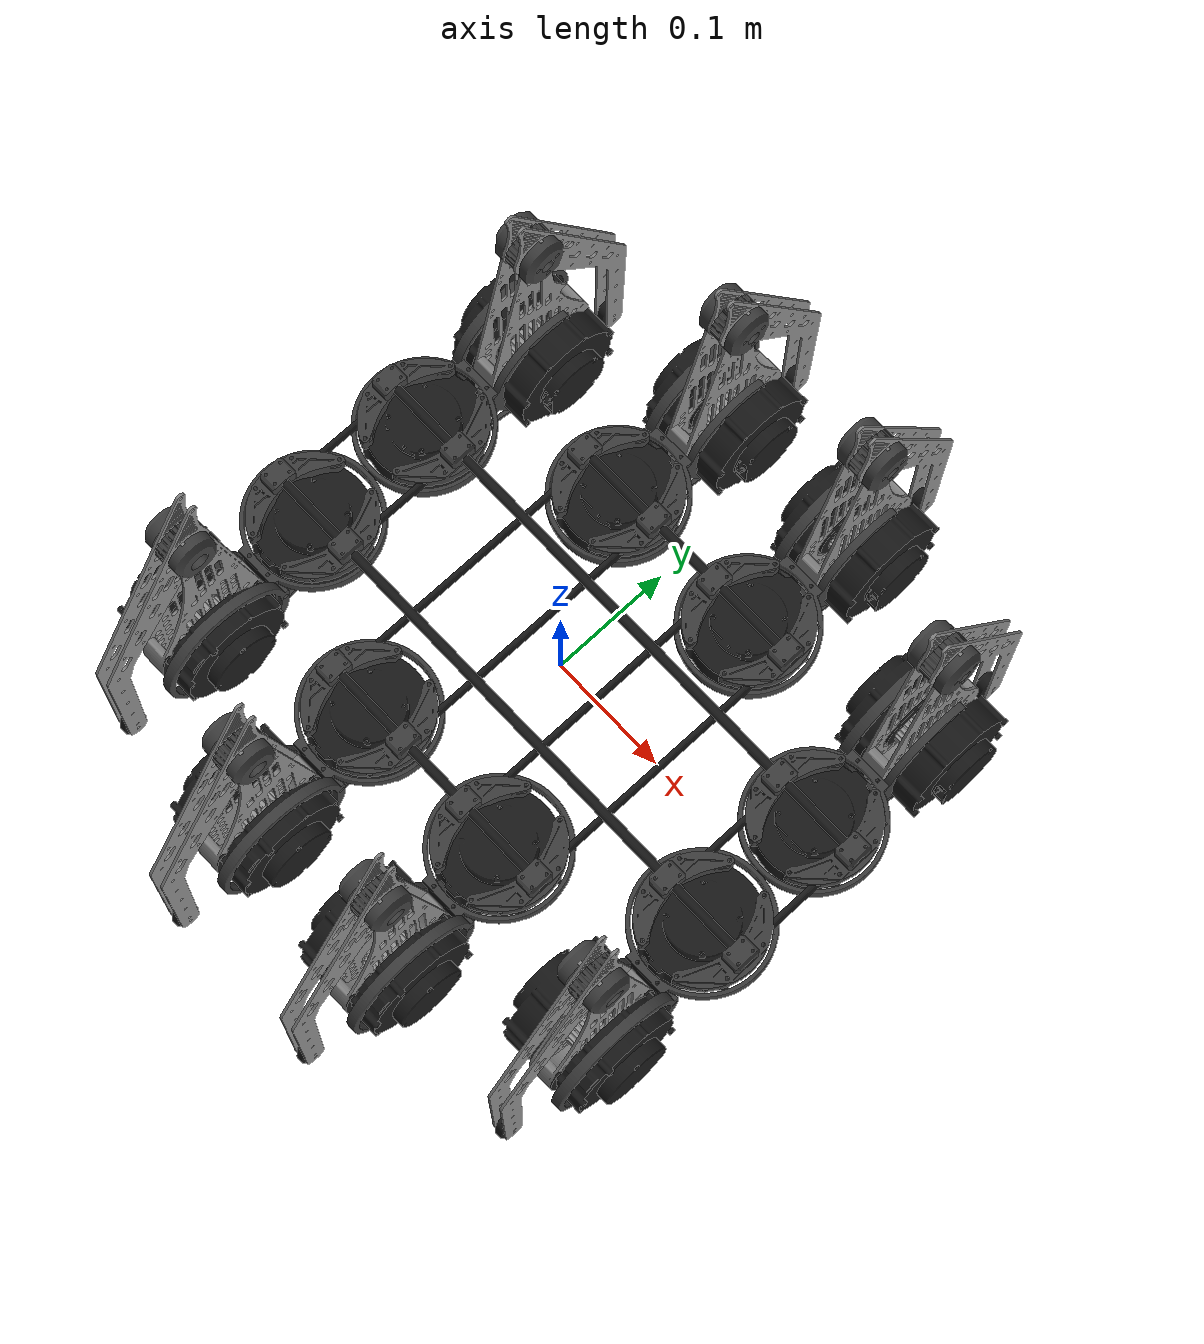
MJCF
<mujoco model="SpiderBot">
    <compiler angle="radian" />
    <default>
        <mesh scale="0.001 0.001 0.001" />
        <geom contype="0" conaffinity="0" group="2" />
        <default class="collision">
            <geom contype="1" conaffinity="1" group="3" pos="0 0 0" mass="0.0" />
        </default>
    </default>
    <asset>
        <mesh name="Body_visual" file="meshes/Body/visual.stl" />
        <mesh name="Femur_visual" file="meshes/Femur/visual.stl" />
        <mesh name="Femur_collision00" file="meshes/Femur/collision00.stl" />
        <mesh name="Motor_visual" file="meshes/Motor/visual.stl" />
        <mesh name="Motor_collision00" file="meshes/Motor/collision00.stl" />
        <mesh name="Motor_collision01" file="meshes/Motor/collision01.stl" />
        <mesh name="Motor_collision02" file="meshes/Motor/collision02.stl" />
        <mesh name="Motor_collision03" file="meshes/Motor/collision03.stl" />
        <mesh name="KneeBearingHolder_visual" file="meshes/KneeBearingHolder/visual.stl" />
        <mesh name="KneeBearingHolder_collision00" file="meshes/KneeBearingHolder/collision00.stl" />
        <mesh name="KneeBearingHolder_collision01" file="meshes/KneeBearingHolder/collision01.stl" />
        <mesh name="MotorPulley_visual" file="meshes/MotorPulley/visual.stl" />
        <mesh name="Tibia_visual" file="meshes/Tibia/visual.stl" />
        <mesh name="Tibia_collision00" file="meshes/Tibia/collision00.stl" />
        <mesh name="Tibia_collision01" file="meshes/Tibia/collision01.stl" />
        <mesh name="Tibia_collision02" file="meshes/Tibia/collision02.stl" />
        <mesh name="Tibia_collision03" file="meshes/Tibia/collision03.stl" />
        <mesh name="Knee_visual" file="meshes/Knee/visual.stl" />
        <mesh name="Foot_visual" file="meshes/Foot/visual.stl" />
        <mesh name="Foot_collision00" file="meshes/Foot/collision00.stl" />
        <mesh name="TibiaBearingTrack_visual" file="meshes/TibiaBearingTrack/visual.stl" />
        <mesh name="TibiaMotorSpacer_visual" file="meshes/TibiaMotorSpacer/visual.stl" />
        <mesh name="Hip_visual" file="meshes/Hip/visual.stl" />
        <mesh name="HipBearingTrack_visual" file="meshes/HipBearingTrack/visual.stl" />
        <mesh name="MainClamp_visual" file="meshes/MainClamp/visual.stl" />
        <mesh name="CrossClamp_visual" file="meshes/CrossClamp/visual.stl" />
        <material name="Body_mat" rgba="0.0980 0.0980 0.0980 1.0000" roughness="0.0775" />
        <material name="Femur_mat" rgba="0.5373 0.5373 0.5373 1.0000" roughness="0.1225" />
        <material name="Motor_mat" rgba="0.0980 0.0980 0.0980 1.0000" roughness="0.0775" />
        <material name="KneeBearingHolder_mat" rgba="0.2471 0.2471 0.2471 1.0000" roughness="0.2600" />
        <material name="MotorPulley_mat" rgba="0.6275 0.6275 0.6275 1.0000" roughness="0.2646" />
        <material name="Tibia_mat" rgba="0.5373 0.5373 0.5373 1.0000" roughness="0.1225" />
        <material name="Knee_mat" rgba="0.2471 0.2471 0.2471 1.0000" roughness="0.2600" />
        <material name="Foot_mat" rgba="0.0980 0.0980 0.0980 1.0000" roughness="0.7071" />
        <material name="TibiaBearingTrack_mat" rgba="0.2471 0.2471 0.2471 1.0000" roughness="0.2600" />
        <material name="TibiaMotorSpacer_mat" rgba="0.0980 0.0980 0.0980 1.0000" roughness="0.7071" />
        <material name="Hip_mat" rgba="0.2471 0.2471 0.2471 1.0000" roughness="0.2600" />
        <material name="HipBearingTrack_mat" rgba="0.2471 0.2471 0.2471 1.0000" roughness="0.2600" />
        <material name="MainClamp_mat" rgba="0.2471 0.2471 0.2471 1.0000" roughness="0.2600" />
        <material name="CrossClamp_mat" rgba="0.2471 0.2471 0.2471 1.0000" roughness="0.2600" />
    </asset>
    <worldbody>
        <body name="Body" pos="0.0 0.0 0.0" quat="1.0 0.0 0.0 0.0">
            <freejoint />
            <geom mesh="Body_visual" name="Body_Body_visual_geom" type="mesh" pos="0 0 0" quat="1 0 0 0" material="Body_mat" />
            <inertial mass="0.18464093644287463" pos="0.0002043264181948041 6.163197729409591e-17 0.007241278293340654" fullinertia="0.0012170529417377895 0.0032623722956095 0.004463635442019566 2.7068691264730745e-19 8.019621781711088e-07 1.3791534859335566e-19" />
            <body name="R1_MainClamp" pos="0.21768105157175574 -0.1646239541111095 -0.06824959828188881" quat="0.9999979914074321 -0.002004290672836025 -1.0166845459493043e-15 -2.0377354456429908e-18">
                <geom mesh="MainClamp_visual" name="R1_MainClamp_MainClamp_visual_geom" type="mesh" pos="0 0 0" quat="1 0 0 0" material="MainClamp_mat" />
                <inertial mass="0.04277320346680055" pos="-0.01107864167782299 0.10936584632552596 0.07185120146554272" fullinertia="2.5569324435957563e-05 4.955460810323098e-05 7.410198303042144e-05 -6.176818167953811e-08 -4.803365145332672e-10 -1.0852179663382676e-07" />
                <body name="R1_CrossClamp" pos="0.0 0.0 0.0" quat="1.0 2.168404344971009e-19 9.860682090334649e-32 1.0089855797698544e-35">
                    <geom mesh="CrossClamp_visual" name="R1_CrossClamp_CrossClamp_visual_geom" type="mesh" pos="0 0 0" quat="1 0 0 0" material="CrossClamp_mat" />
                    <inertial mass="0.0060873366326105955" pos="-0.011076095384506187 0.10937852181993965 0.08220436514827456" fullinertia="3.569640975298384e-07 8.628331172516439e-06 8.861345261438724e-06 -2.399837145244117e-08 -9.43913792177835e-11 -1.0651462527273285e-09" />
                </body>
                <body name="R1_Hip-assembly_Motor" pos="-0.011076386363475165 0.10966822722227194 0.01505997107270793" quat="-0.0014172475262309893 0.707105360897122 0.001417247526231073 -0.7071053608971223">
                    <geom mesh="Motor_visual" name="R1_Hip-assembly_Motor_Motor_visual_geom" type="mesh" pos="0 0 0" quat="1 0 0 0" material="Motor_mat" />
                    <geom mesh="Motor_collision00" name="R1_Hip-assembly_Motor_Motor_collision00_geom" type="mesh" pos="0 0 0" quat="1 0 0 0" class="collision" />
                    <geom mesh="Motor_collision01" name="R1_Hip-assembly_Motor_Motor_collision01_geom" type="mesh" pos="0 0 0" quat="1 0 0 0" class="collision" />
                    <geom mesh="Motor_collision02" name="R1_Hip-assembly_Motor_Motor_collision02_geom" type="mesh" pos="0 0 0" quat="1 0 0 0" class="collision" />
                    <geom mesh="Motor_collision03" name="R1_Hip-assembly_Motor_Motor_collision03_geom" type="mesh" pos="0 0 0" quat="1 0 0 0" class="collision" />
                    <inertial mass="0.4096463210987154" pos="-0.03569820729651781 0.00047016950890322614 -5.891982746499138e-06" fullinertia="0.0004025220023127328 0.00022651206716561785 0.00023297814211205656 1.5369569971653381e-06 -5.181750872317603e-08 -2.6262635187278443e-08" />
                    <body name="R1_Hip" pos="0.014620638666750283 0.1072497856676494 -0.010329361333291907" quat="1.269974271615229e-15 -0.7071067811865472 1.1023373026774868e-15 0.7071067811865478">
                        <joint type="hinge" name="R1_Hip" axis="2.04862431470163e-15 2.5916768731093498e-15 1.0" pos="-0.010329026541572441 0.10725002467289509 0.035250000000043864" range="-1.396263 1.396263" limited="true" />
                        <geom mesh="Hip_visual" name="R1_Hip_Hip_visual_geom" type="mesh" pos="0 0 0" quat="1 0 0 0" material="Hip_mat" />
                        <inertial mass="0.05147716268131095" pos="-0.012440514153362177 0.04641593719115884 0.028839071087162924" fullinertia="0.00010836979882393105 3.638569500873875e-05 8.716939400280418e-05 -2.872480946096444e-06 3.971226369733437e-06 -1.40764156506885e-05" />
                        <body name="R1_HipBearingTrack" pos="0.0007470250301832238 -0.0024779294382145166 4.017181553184202e-07" quat="0.9999979914074321 -0.0020042906728373207 7.502708268926203e-18 6.130652355437454e-17">
                            <geom mesh="HipBearingTrack_visual" name="R1_HipBearingTrack_HipBearingTrack_visual_geom" type="mesh" pos="0 0 0" quat="1 0 0 0" material="HipBearingTrack_mat" />
                            <inertial mass="0.011498241565854663" pos="-0.010937303304392982 0.1083863442949837 0.060712687282961336" fullinertia="1.7153250560057054e-05 1.5343996736285954e-05 3.234145154765093e-05 8.828736129535754e-08 2.80188333204562e-09 1.1199274998521652e-07" />
                        </body>
                        <body name="R1_Femur-assembly_Motor" pos="3.552713678800501e-17 -3.1974423109204507e-16 0.05000000000000131" quat="-6.114900252818196e-17 1.0 6.126241564798602e-17 -2.2709978787097704e-29">
                            <geom mesh="Motor_visual" name="R1_Femur-assembly_Motor_Motor_visual_geom" type="mesh" pos="0 0 0" quat="1 0 0 0" material="Motor_mat" />
                            <geom mesh="Motor_collision00" name="R1_Femur-assembly_Motor_Motor_collision00_geom" type="mesh" pos="0 0 0" quat="1 0 0 0" class="collision" />
                            <geom mesh="Motor_collision01" name="R1_Femur-assembly_Motor_Motor_collision01_geom" type="mesh" pos="0 0 0" quat="1 0 0 0" class="collision" />
                            <geom mesh="Motor_collision02" name="R1_Femur-assembly_Motor_Motor_collision02_geom" type="mesh" pos="0 0 0" quat="1 0 0 0" class="collision" />
                            <geom mesh="Motor_collision03" name="R1_Femur-assembly_Motor_Motor_collision03_geom" type="mesh" pos="0 0 0" quat="1 0 0 0" class="collision" />
                            <inertial mass="0.4096463210987154" pos="-0.03569820729651777 0.0004701695089032045 -5.891982746489858e-06" fullinertia="0.000402522002312734 0.00022651206716561866 0.0002329781421120602 1.5369569971619705e-06 -5.181750872274396e-08 -2.626263518720765e-08" />
                            <body name="R1_Femur" pos="-3.552713678800501e-17 -2.1316282072803005e-16 0.04999999999999991" quat="-2.609024107869118e-15 0.9999999999999999 4.0331181728202185e-35 1.2883537514623674e-31">
                                <joint type="hinge" name="R1_Femur" axis="-1.0 -5.78943166969219e-20 2.048624314701585e-15" pos="-0.0206290265415724 2.4672895484718057e-08 0.05000000000004279" range="-1.570796 0.0" limited="true" />
                                <geom mesh="Femur_visual" name="R1_Femur_Femur_visual_geom" type="mesh" pos="0 0 0" quat="1 0 0 0" material="Femur_mat" />
                                <geom mesh="Femur_collision00" name="R1_Femur_Femur_collision00_geom" type="mesh" pos="0 0 0" quat="1 0 0 0" class="collision" />
                                <inertial mass="0.24579016961382127" pos="-0.01053259980046678 0.0011709274947812817 0.05735512283399398" fullinertia="0.0009694518744856736 0.0007430878661755284 0.0002519361498616281 -1.1656213079474316e-07 -5.59202008469493e-07 -2.128645529084145e-05" />
                                <body name="R1_KneeBearingHolder" pos="0.0007470250301832238 -0.0016160678817224296 -7.8038589705276e-06" quat="1.0 0.0 1.4804634561769345e-17 7.358128197847213e-20">
                                    <geom mesh="KneeBearingHolder_visual" name="R1_KneeBearingHolder_KneeBearingHolder_visual_geom" type="mesh" pos="0 0 0" quat="1 0 0 0" material="KneeBearingHolder_mat" />
                                    <geom mesh="KneeBearingHolder_collision00" name="R1_KneeBearingHolder_KneeBearingHolder_collision00_geom" type="mesh" pos="0 0 0" quat="1 0 0 0" class="collision" />
                                    <geom mesh="KneeBearingHolder_collision01" name="R1_KneeBearingHolder_KneeBearingHolder_collision01_geom" type="mesh" pos="0 0 0" quat="1 0 0 0" class="collision" />
                                    <inertial mass="0.030925555853756816" pos="-0.01119404186844089 0.0015266506285498962 0.21513970595587004" fullinertia="3.844289443836546e-06 8.286900098701446e-06 7.876924971833479e-06 8.00838512258504e-10 -1.3673282818401324e-09 8.394524227811552e-08" />
                                </body>
                                <body name="R1_TibiaMotorSpacer" pos="0.0 0.0 0.0" quat="1.0 0.0 0.0 -7.821578647613801e-46">
                                    <geom mesh="TibiaMotorSpacer_visual" name="R1_TibiaMotorSpacer_TibiaMotorSpacer_visual_geom" type="mesh" pos="0 0 0" quat="1 0 0 0" material="TibiaMotorSpacer_mat" />
                                    <inertial mass="0.01707375831954851" pos="0.0011206386667055206 -3.323214932799273e-06 0.029480584226304365" fullinertia="2.9215193206498784e-05 7.474279434871228e-06 2.174731643099742e-05 4.874380184415562e-24 3.891123458060769e-20 1.7649428501173587e-09" />
                                    <body name="R1_Tibia-assembly_Motor" pos="-0.024258722666588427 8.988365607365268e-15 0.04999990988664587" quat="-2.3121695236544695e-16 7.204649433140694e-16 0.3826834323650902 0.9238795325112871">
                                        <geom mesh="Motor_visual" name="R1_Tibia-assembly_Motor_Motor_visual_geom" type="mesh" pos="0 0 0" quat="1 0 0 0" material="Motor_mat" />
                                        <geom mesh="Motor_collision00" name="R1_Tibia-assembly_Motor_Motor_collision00_geom" type="mesh" pos="0 0 0" quat="1 0 0 0" class="collision" />
                                        <geom mesh="Motor_collision01" name="R1_Tibia-assembly_Motor_Motor_collision01_geom" type="mesh" pos="0 0 0" quat="1 0 0 0" class="collision" />
                                        <geom mesh="Motor_collision02" name="R1_Tibia-assembly_Motor_Motor_collision02_geom" type="mesh" pos="0 0 0" quat="1 0 0 0" class="collision" />
                                        <geom mesh="Motor_collision03" name="R1_Tibia-assembly_Motor_Motor_collision03_geom" type="mesh" pos="0 0 0" quat="1 0 0 0" class="collision" />
                                        <inertial mass="0.4096463210987154" pos="-0.03569820729651784 0.0004701695089032175 -5.891982746474123e-06" fullinertia="0.000402522002312733 0.00022651206716561858 0.00023297814211205748 1.5369569971656411e-06 -5.1817508723597274e-08 -2.626263518639545e-08" />
                                        <body name="R1_MotorPulley" pos="-0.007129361333247992 -0.03304157594374691 -0.019714907448652303" quat="3.138003026719071e-16 2.139445958814906e-15 0.7071067811865582 0.7071067811865591">
                                            <geom mesh="MotorPulley_visual" name="R1_MotorPulley_MotorPulley_visual_geom" type="mesh" pos="0 0 0" quat="1 0 0 0" material="MotorPulley_mat" />
                                            <inertial mass="0.08827799534918106" pos="0.0068634644760760125 0.019714907448616516 0.03304157594370562" fullinertia="1.3695013569533796e-05 8.182915999385794e-06 8.182916000116651e-06 -3.542428357736684e-18 -6.001558671222379e-18 -9.627614888300853e-17" />
                                        </body>
                                    </body>
                                </body>
                                <body name="R1_Tibia" pos="0.0 0.0 0.0" quat="1.0 0.0 0.0 -7.821578647613801e-46">
                                    <joint type="hinge" name="R1_Tibia" axis="-1.0 -5.78943166969219e-20 2.048624314701585e-15" pos="-0.0016290265415720743 2.4672896793502965e-08 0.21500000000004274" range="-0.20944 2.268928" limited="true" />
                                    <geom mesh="Tibia_visual" name="R1_Tibia_Tibia_visual_geom" type="mesh" pos="0 0 0" quat="1 0 0 0" material="Tibia_mat" />
                                    <geom mesh="Tibia_collision00" name="R1_Tibia_Tibia_collision00_geom" type="mesh" pos="0 0 0" quat="1 0 0 0" class="collision" />
                                    <geom mesh="Tibia_collision01" name="R1_Tibia_Tibia_collision01_geom" type="mesh" pos="0 0 0" quat="1 0 0 0" class="collision" />
                                    <geom mesh="Tibia_collision02" name="R1_Tibia_Tibia_collision02_geom" type="mesh" pos="0 0 0" quat="1 0 0 0" class="collision" />
                                    <geom mesh="Tibia_collision03" name="R1_Tibia_Tibia_collision03_geom" type="mesh" pos="0 0 0" quat="1 0 0 0" class="collision" />
                                    <inertial mass="0.07204696639616184" pos="-0.010129361333294342 -0.0448480988551342 0.1311976864864586" fullinertia="0.0005149405353785741 0.0004336853473697241 8.649060090030344e-05 -3.5204655393729474e-19 4.2331960257993766e-19 -0.0001718476421589163" />
                                    <body name="R1_Foot" pos="0.0 0.0 0.0" quat="1.0 0.0 0.0 -7.821578647613801e-46">
                                        <geom mesh="Foot_visual" name="R1_Foot_Foot_visual_geom" type="mesh" pos="0 0 0" quat="1 0 0 0" material="Foot_mat" />
                                        <geom mesh="Foot_collision00" name="R1_Foot_Foot_collision00_geom" type="mesh" pos="0 0 0" quat="1 0 0 0" class="collision" />
                                        <inertial mass="0.004227311785411664" pos="-0.010129361333294194 -0.08110044236751457 -0.02208504803789865" fullinertia="3.397896334932744e-07 2.6675812760492464e-07 1.365451113407505e-07 2.7106356244018384e-20 1.3136155449483794e-20 6.334513176574432e-10" />
                                    </body>
                                    <body name="R1_Knee" pos="-0.015129361333294433 -0.01971490744867147 0.18195842405632334" quat="1.0 0.0 -7.098466027833436e-18 2.8947158356597294e-20">
                                        <geom mesh="Knee_visual" name="R1_Knee_Knee_visual_geom" type="mesh" pos="0 0 0" quat="1 0 0 0" material="Knee_mat" />
                                        <inertial mass="0.011943740884513946" pos="0.004999999999999962 0.019714907448696316 0.033041575943743906" fullinertia="1.5387029252575358e-06 1.0362479220743038e-06 1.0362479223933845e-06 1.0842021724847578e-19 -1.0945669210399895e-19 -3.5778671692019113e-17" />
                                    </body>
                                </body>
                            </body>
                        </body>
                        <body name="R1_TibiaBearingTrack" pos="0.0 -1.0658141036401502e-16 1.3766765505351941e-15" quat="1.0 2.6701731103973003e-15 2.2876966251409342e-29 6.1262415647986e-17">
                            <geom mesh="TibiaBearingTrack_visual" name="R1_TibiaBearingTrack_TibiaBearingTrack_visual_geom" type="mesh" pos="0 0 0" quat="1 0 0 0" material="TibiaBearingTrack_mat" />
                            <inertial mass="0.017229748042217916" pos="0.012537173999850507 0.005852064706060482 0.040782785041914744" fullinertia="4.8744379756449736e-05 2.505702208782712e-05 2.389672649521925e-05 2.021266320552256e-09 -4.0295101591736685e-09 9.6862291695154e-07" />
                        </body>
                    </body>
                </body>
            </body>
            <body name="L1_MainClamp" pos="0.19552827884480486 0.16462395411110975 -0.06824959828188862" quat="3.304566878248689e-18 1.648743011932669e-15 -0.0020042906728360193 0.9999979914074331">
                <geom mesh="MainClamp_visual" name="L1_MainClamp_MainClamp_visual_geom" type="mesh" pos="0 0 0" quat="1 0 0 0" material="MainClamp_mat" />
                <inertial mass="0.04277320346680055" pos="-0.011078641677823083 0.1093658463255267 0.07185120146554272" fullinertia="2.55693244359594e-05 4.9554608103233065e-05 7.41019830304171e-05 -6.176818167937589e-08 -4.803365145458032e-10 -1.0852179663385826e-07" />
                <body name="L1_CrossClamp" pos="0.0 3.552713678800501e-17 0.0" quat="1.0 2.1689618408400908e-19 9.865514810942556e-32 -1.6059710305357113e-33">
                    <geom mesh="CrossClamp_visual" name="L1_CrossClamp_CrossClamp_visual_geom" type="mesh" pos="0 0 0" quat="1 0 0 0" material="CrossClamp_mat" />
                    <inertial mass="0.0060873366326105955" pos="-0.011076095384506338 0.10937852181994043 0.08220436514827456" fullinertia="3.569640975301696e-07 8.628331172516933e-06 8.861345261438236e-06 -2.399837145242778e-08 -9.439137922053112e-11 -1.065146252729532e-09" />
                </body>
                <body name="L1_Hip-assembly_Motor" pos="-0.011076386363475165 0.109668227222272 0.015059971072707939" quat="-0.0014172475262309893 0.707105360897122 0.001417247526231073 -0.7071053608971223">
                    <geom mesh="Motor_visual" name="L1_Hip-assembly_Motor_Motor_visual_geom" type="mesh" pos="0 0 0" quat="1 0 0 0" material="Motor_mat" />
                    <geom mesh="Motor_collision00" name="L1_Hip-assembly_Motor_Motor_collision00_geom" type="mesh" pos="0 0 0" quat="1 0 0 0" class="collision" />
                    <geom mesh="Motor_collision01" name="L1_Hip-assembly_Motor_Motor_collision01_geom" type="mesh" pos="0 0 0" quat="1 0 0 0" class="collision" />
                    <geom mesh="Motor_collision02" name="L1_Hip-assembly_Motor_Motor_collision02_geom" type="mesh" pos="0 0 0" quat="1 0 0 0" class="collision" />
                    <geom mesh="Motor_collision03" name="L1_Hip-assembly_Motor_Motor_collision03_geom" type="mesh" pos="0 0 0" quat="1 0 0 0" class="collision" />
                    <inertial mass="0.4096463210987154" pos="-0.03569820729651781 0.00047016950890323665 -5.891982746508759e-06" fullinertia="0.0004025220023127293 0.00022651206716561948 0.0002329781421120636 1.5369569971652288e-06 -5.181750872296188e-08 -2.6262635187276683e-08" />
                    <body name="L1_Hip" pos="0.014620638666750221 0.1072497856676494 -0.010329361333291872" quat="1.2604678524317923e-15 -0.7071067811865474 1.1026439613608192e-15 0.7071067811865477">
                        <joint type="hinge" name="L1_Hip" axis="3.3127437857693405e-15 2.5925442348473382e-15 0.9999999999999998" pos="-0.010329696125011792 0.10725002467289564 0.03525000000004361" range="-1.396263 1.396263" limited="true" />
                        <geom mesh="Hip_visual" name="L1_Hip_Hip_visual_geom" type="mesh" pos="0 0 0" quat="1 0 0 0" material="Hip_mat" />
                        <inertial mass="0.05147716268131095" pos="-0.012440514153362255 0.04641593719115915 0.02883907108716291" fullinertia="0.00010836979882393322 3.6385695008739414e-05 8.71693940028037e-05 -2.8724809460964827e-06 3.971226369733532e-06 -1.4076415650688591e-05" />
                        <body name="L1_HipBearingTrack" pos="0.0007470250301832948 -0.0024779294382145166 4.0171815524736586e-07" quat="0.9999979914074321 -0.002004290672837315 7.530523389587777e-18 4.7428763621381587e-17">
                            <geom mesh="HipBearingTrack_visual" name="L1_HipBearingTrack_HipBearingTrack_visual_geom" type="mesh" pos="0 0 0" quat="1 0 0 0" material="HipBearingTrack_mat" />
                            <inertial mass="0.011498241565854663" pos="-0.01093730330439305 0.10838634429498449 0.06071268728296133" fullinertia="1.715325056005759e-05 1.5343996736286496e-05 3.234145154764995e-05 8.828736129535839e-08 2.801883332044499e-09 1.1199274998524049e-07" />
                        </body>
                        <body name="L1_Femur-assembly_Motor" pos="0.0 -2.486899575160351e-16 0.0500000000000013" quat="-6.114900252818165e-17 1.0000000000000002 6.126241564798602e-17 -2.277835863825671e-29">
                            <geom mesh="Motor_visual" name="L1_Femur-assembly_Motor_Motor_visual_geom" type="mesh" pos="0 0 0" quat="1 0 0 0" material="Motor_mat" />
                            <geom mesh="Motor_collision00" name="L1_Femur-assembly_Motor_Motor_collision00_geom" type="mesh" pos="0 0 0" quat="1 0 0 0" class="collision" />
                            <geom mesh="Motor_collision01" name="L1_Femur-assembly_Motor_Motor_collision01_geom" type="mesh" pos="0 0 0" quat="1 0 0 0" class="collision" />
                            <geom mesh="Motor_collision02" name="L1_Femur-assembly_Motor_Motor_collision02_geom" type="mesh" pos="0 0 0" quat="1 0 0 0" class="collision" />
                            <geom mesh="Motor_collision03" name="L1_Femur-assembly_Motor_Motor_collision03_geom" type="mesh" pos="0 0 0" quat="1 0 0 0" class="collision" />
                            <inertial mass="0.4096463210987154" pos="-0.03569820729651808 0.00047016950890320505 -5.891982746488355e-06" fullinertia="0.00040252200231273853 0.00022651206716561324 0.0002329781421120462 1.5369569971654554e-06 -5.1817508723830863e-08 -2.6262635186772103e-08" />
                            <body name="L1_Femur" pos="0.0 -1.7763568394002506e-16 0.04999999999999991" quat="-2.609024107869114e-15 0.9999999999999998 -1.1425942351868409e-33 1.3356125988095916e-45">
                                <joint type="hinge" name="L1_Femur" axis="-1.0000000000000036 2.7697681298942016e-17 3.3127437857692817e-15" pos="-0.020629696125011743 2.4672895707378696e-08 0.05000000000004255" range="-1.570796 0.0" limited="true" />
                                <geom mesh="Femur_visual" name="L1_Femur_Femur_visual_geom" type="mesh" pos="0 0 0" quat="1 0 0 0" material="Femur_mat" />
                                <geom mesh="Femur_collision00" name="L1_Femur_Femur_collision00_geom" type="mesh" pos="0 0 0" quat="1 0 0 0" class="collision" />
                                <inertial mass="0.24579016961382127" pos="-0.010532599800466887 0.0011709274947812856 0.05735512283399395" fullinertia="0.0009694518744856953 0.0007430878661755485 0.00025193614986163495 -1.165621307930424e-07 -5.592020084688846e-07 -2.128645529084135e-05" />
                                <body name="L1_KneeBearingHolder" pos="0.0007470250301832948 -0.001616067881722465 -7.80385897058089e-06" quat="1.0 6.5052130349118895e-18 1.480463456176788e-17 -1.380420652583594e-17">
                                    <geom mesh="KneeBearingHolder_visual" name="L1_KneeBearingHolder_KneeBearingHolder_visual_geom" type="mesh" pos="0 0 0" quat="1 0 0 0" material="KneeBearingHolder_mat" />
                                    <geom mesh="KneeBearingHolder_collision00" name="L1_KneeBearingHolder_KneeBearingHolder_collision00_geom" type="mesh" pos="0 0 0" quat="1 0 0 0" class="collision" />
                                    <geom mesh="KneeBearingHolder_collision01" name="L1_KneeBearingHolder_KneeBearingHolder_collision01_geom" type="mesh" pos="0 0 0" quat="1 0 0 0" class="collision" />
                                    <inertial mass="0.030925555853756816" pos="-0.011194041868441014 0.001526650628549866 0.21513970595587004" fullinertia="3.844289443842645e-06 8.286900098709744e-06 7.876924971835647e-06 8.00838513342818e-10 -1.3673282821603001e-09 8.394524227800718e-08" />
                                </body>
                                <body name="L1_TibiaMotorSpacer" pos="0.0 0.0 0.0" quat="1.0 9.186685834726984e-32 2.664201004600939e-32 8.99858448021955e-35">
                                    <geom mesh="TibiaMotorSpacer_visual" name="L1_TibiaMotorSpacer_TibiaMotorSpacer_visual_geom" type="mesh" pos="0 0 0" quat="1 0 0 0" material="TibiaMotorSpacer_mat" />
                                    <inertial mass="0.01707375831954851" pos="0.0011206386667055263 -3.3232149327992893e-06 0.02948058422630435" fullinertia="2.921519320649932e-05 7.474279434871382e-06 2.174731643099763e-05 1.0782389115121645e-19 5.65760494403035e-20 1.764942850117376e-09" />
                                    <body name="L1_Tibia-assembly_Motor" pos="-0.02425872266658846 9.023892744153272e-15 0.04999990988664589" quat="-2.312169523654469e-16 7.204649433140692e-16 0.38268343236509034 0.9238795325112871">
                                        <geom mesh="Motor_visual" name="L1_Tibia-assembly_Motor_Motor_visual_geom" type="mesh" pos="0 0 0" quat="1 0 0 0" material="Motor_mat" />
                                        <geom mesh="Motor_collision00" name="L1_Tibia-assembly_Motor_Motor_collision00_geom" type="mesh" pos="0 0 0" quat="1 0 0 0" class="collision" />
                                        <geom mesh="Motor_collision01" name="L1_Tibia-assembly_Motor_Motor_collision01_geom" type="mesh" pos="0 0 0" quat="1 0 0 0" class="collision" />
                                        <geom mesh="Motor_collision02" name="L1_Tibia-assembly_Motor_Motor_collision02_geom" type="mesh" pos="0 0 0" quat="1 0 0 0" class="collision" />
                                        <geom mesh="Motor_collision03" name="L1_Tibia-assembly_Motor_Motor_collision03_geom" type="mesh" pos="0 0 0" quat="1 0 0 0" class="collision" />
                                        <inertial mass="0.4096463210987154" pos="-0.03569820729651811 0.00047016950890322007 -5.891982746474603e-06" fullinertia="0.0004025220023127393 0.0002265120671656208 0.00023297814211206022 1.536956997163503e-06 -5.181750872083914e-08 -2.6262635185467344e-08" />
                                        <body name="L1_MotorPulley" pos="-0.007129361333247921 -0.0330415759437469 -0.019714907448652303" quat="3.138003026719068e-16 2.1394459588149053e-15 0.7071067811865583 0.7071067811865591">
                                            <geom mesh="MotorPulley_visual" name="L1_MotorPulley_MotorPulley_visual_geom" type="mesh" pos="0 0 0" quat="1 0 0 0" material="MotorPulley_mat" />
                                            <inertial mass="0.08827799534918106" pos="0.006863464476076049 0.019714907448616457 0.03304157594370566" fullinertia="1.3695013569534761e-05 8.18291599938517e-06 8.182916000116026e-06 -3.854122306959214e-18 -5.699718891200217e-18 -9.738860480010528e-17" />
                                        </body>
                                    </body>
                                </body>
                                <body name="L1_Tibia" pos="0.0 0.0 0.0" quat="1.0 9.186685834726984e-32 2.664201004600939e-32 8.99858448021955e-35">
                                    <joint type="hinge" name="L1_Tibia" axis="-1.0000000000000036 2.7697681298942016e-17 3.3127437857692817e-15" pos="-0.0016296961250111416 2.4672897015779366e-08 0.21500000000004243" range="-0.20944 2.268928" limited="true" />
                                    <geom mesh="Tibia_visual" name="L1_Tibia_Tibia_visual_geom" type="mesh" pos="0 0 0" quat="1 0 0 0" material="Tibia_mat" />
                                    <geom mesh="Tibia_collision00" name="L1_Tibia_Tibia_collision00_geom" type="mesh" pos="0 0 0" quat="1 0 0 0" class="collision" />
                                    <geom mesh="Tibia_collision01" name="L1_Tibia_Tibia_collision01_geom" type="mesh" pos="0 0 0" quat="1 0 0 0" class="collision" />
                                    <geom mesh="Tibia_collision02" name="L1_Tibia_Tibia_collision02_geom" type="mesh" pos="0 0 0" quat="1 0 0 0" class="collision" />
                                    <geom mesh="Tibia_collision03" name="L1_Tibia_Tibia_collision03_geom" type="mesh" pos="0 0 0" quat="1 0 0 0" class="collision" />
                                    <inertial mass="0.07204696639616184" pos="-0.010129361333294392 -0.04484809885513448 0.13119768648645852" fullinertia="0.0005149405353785904 0.00043368534736973894 8.649060090030339e-05 7.295048180202195e-19 9.611401402874215e-19 -0.00017184764215891725" />
                                    <body name="L1_Foot" pos="0.0 0.0 0.0" quat="1.0 9.186685834726984e-32 2.664201004600939e-32 8.99858448021955e-35">
                                        <geom mesh="Foot_visual" name="L1_Foot_Foot_visual_geom" type="mesh" pos="0 0 0" quat="1 0 0 0" material="Foot_mat" />
                                        <geom mesh="Foot_collision00" name="L1_Foot_Foot_collision00_geom" type="mesh" pos="0 0 0" quat="1 0 0 0" class="collision" />
                                        <inertial mass="0.004227311785411664" pos="-0.01012936133329426 -0.08110044236751507 -0.022085048037898628" fullinertia="3.3978963349333104e-07 2.6675812760498055e-07 1.3654511134069623e-07 7.565854158460646e-26 2.6431774829517632e-20 6.334513176845499e-10" />
                                    </body>
                                    <body name="L1_Knee" pos="-0.01512936133329447 -0.01971490744867147 0.18195842405632334" quat="1.0 -5.227455351553062e-31 -7.098466027833417e-18 2.894715835659655e-20">
                                        <geom mesh="Knee_visual" name="L1_Knee_Knee_visual_geom" type="mesh" pos="0 0 0" quat="1 0 0 0" material="Knee_mat" />
                                        <inertial mass="0.011943740884513946" pos="0.005000000000000057 0.01971490744869649 0.03304157594374392" fullinertia="1.5387029252577637e-06 1.0362479220742021e-06 1.0362479223931672e-06 -1.3945927952929085e-23 5.253847061636937e-20 -3.577867169201923e-17" />
                                    </body>
                                </body>
                            </body>
                        </body>
                        <body name="L1_TibiaBearingTrack" pos="0.0 -7.105427357601002e-17 1.3677947663381929e-15" quat="1.0 2.6701731103972968e-15 2.3002215874607978e-29 6.126241564798602e-17">
                            <geom mesh="TibiaBearingTrack_visual" name="L1_TibiaBearingTrack_TibiaBearingTrack_visual_geom" type="mesh" pos="0 0 0" quat="1 0 0 0" material="TibiaBearingTrack_mat" />
                            <inertial mass="0.017229748042217916" pos="0.012537173999850604 0.005852064706060518 0.04078278504191473" fullinertia="4.874437975645063e-05 2.5057022087827275e-05 2.3896726495218804e-05 2.0212663205528364e-09 -4.029510159164408e-09 9.686229169515156e-07" />
                        </body>
                    </body>
                </body>
            </body>
            <body name="R2_MainClamp" pos="0.07968105157175574 -0.2326239541111095 -0.06824959828188881" quat="0.9999979914074321 -0.002004290672836025 -1.0166845459493043e-15 -2.0377354456429908e-18">
                <geom mesh="MainClamp_visual" name="R2_MainClamp_MainClamp_visual_geom" type="mesh" pos="0 0 0" quat="1 0 0 0" material="MainClamp_mat" />
                <inertial mass="0.04277320346680055" pos="-0.01107864167782299 0.10936584632552594 0.07185120146554272" fullinertia="2.556932443595751e-05 4.955460810323087e-05 7.410198303042101e-05 -6.176818167942967e-08 -4.803365145379147e-10 -1.0852179663382631e-07" />
                <body name="R2_CrossClamp" pos="0.0 0.0 0.0" quat="1.0 2.168404344971009e-19 9.860682090334649e-32 1.0089855797698544e-35">
                    <geom mesh="CrossClamp_visual" name="R2_CrossClamp_CrossClamp_visual_geom" type="mesh" pos="0 0 0" quat="1 0 0 0" material="CrossClamp_mat" />
                    <inertial mass="0.0060873366326105955" pos="-0.011076095384506213 0.10937852181993965 0.08220436514827456" fullinertia="3.569640975298452e-07 8.628331172516496e-06 8.861345261438805e-06 -2.3998371452447943e-08 -9.439137921865767e-11 -1.0651462527282748e-09" />
                </body>
                <body name="R2_Hip-assembly_Motor" pos="-0.011076386363475165 0.10966822722227194 0.01505997107270793" quat="-0.0014172475262309893 0.707105360897122 0.001417247526231073 -0.7071053608971223">
                    <geom mesh="Motor_visual" name="R2_Hip-assembly_Motor_Motor_visual_geom" type="mesh" pos="0 0 0" quat="1 0 0 0" material="Motor_mat" />
                    <geom mesh="Motor_collision00" name="R2_Hip-assembly_Motor_Motor_collision00_geom" type="mesh" pos="0 0 0" quat="1 0 0 0" class="collision" />
                    <geom mesh="Motor_collision01" name="R2_Hip-assembly_Motor_Motor_collision01_geom" type="mesh" pos="0 0 0" quat="1 0 0 0" class="collision" />
                    <geom mesh="Motor_collision02" name="R2_Hip-assembly_Motor_Motor_collision02_geom" type="mesh" pos="0 0 0" quat="1 0 0 0" class="collision" />
                    <geom mesh="Motor_collision03" name="R2_Hip-assembly_Motor_Motor_collision03_geom" type="mesh" pos="0 0 0" quat="1 0 0 0" class="collision" />
                    <inertial mass="0.4096463210987154" pos="-0.03569820729651781 0.00047016950890323497 -5.891982746481375e-06" fullinertia="0.0004025220023127328 0.00022651206716561525 0.00023297814211205526 1.536956997165284e-06 -5.181750872285077e-08 -2.6262635187278443e-08" />
                    <body name="R2_Hip" pos="0.014620638666750275 0.10724978566764942 -0.010329361333291907" quat="1.269974271615229e-15 -0.7071067811865472 1.1023373026774868e-15 0.7071067811865478">
                        <joint type="hinge" name="R2_Hip" axis="2.04862431470163e-15 2.5916768731093498e-15 1.0" pos="-0.010329026541572441 0.10725002467289509 0.035250000000043864" range="-1.396263 1.396263" limited="true" />
                        <geom mesh="Hip_visual" name="R2_Hip_Hip_visual_geom" type="mesh" pos="0 0 0" quat="1 0 0 0" material="Hip_mat" />
                        <inertial mass="0.05147716268131095" pos="-0.012440514153362177 0.04641593719115886 0.028839071087162924" fullinertia="0.00010836979882393116 3.638569500873897e-05 8.716939400280505e-05 -2.8724809460960105e-06 3.97122636973341e-06 -1.4076415650688608e-05" />
                        <body name="R2_HipBearingTrack" pos="0.0007470250301832416 -0.0024779294382145166 4.017181553184202e-07" quat="0.9999979914074321 -0.0020042906728373207 7.502708268926203e-18 6.130652355437454e-17">
                            <geom mesh="HipBearingTrack_visual" name="R2_HipBearingTrack_HipBearingTrack_visual_geom" type="mesh" pos="0 0 0" quat="1 0 0 0" material="HipBearingTrack_mat" />
                            <inertial mass="0.011498241565854663" pos="-0.010937303304392973 0.1083863442949837 0.060712687282961336" fullinertia="1.7153250560057026e-05 1.5343996736285913e-05 3.234145154765098e-05 8.828736129535754e-08 2.801883332043926e-09 1.1199274998522122e-07" />
                        </body>
                        <body name="R2_Femur-assembly_Motor" pos="8.881784197001253e-18 -3.1974423109204507e-16 0.05000000000000131" quat="-6.114900252818196e-17 1.0 6.126241564798602e-17 -2.2709978787097704e-29">
                            <geom mesh="Motor_visual" name="R2_Femur-assembly_Motor_Motor_visual_geom" type="mesh" pos="0 0 0" quat="1 0 0 0" material="Motor_mat" />
                            <geom mesh="Motor_collision00" name="R2_Femur-assembly_Motor_Motor_collision00_geom" type="mesh" pos="0 0 0" quat="1 0 0 0" class="collision" />
                            <geom mesh="Motor_collision01" name="R2_Femur-assembly_Motor_Motor_collision01_geom" type="mesh" pos="0 0 0" quat="1 0 0 0" class="collision" />
                            <geom mesh="Motor_collision02" name="R2_Femur-assembly_Motor_Motor_collision02_geom" type="mesh" pos="0 0 0" quat="1 0 0 0" class="collision" />
                            <geom mesh="Motor_collision03" name="R2_Femur-assembly_Motor_Motor_collision03_geom" type="mesh" pos="0 0 0" quat="1 0 0 0" class="collision" />
                            <inertial mass="0.4096463210987154" pos="-0.03569820729651777 0.00047016950890324007 -5.891982746489858e-06" fullinertia="0.0004025220023127288 0.00022651206716561866 0.00023297814211205325 1.53695699716544e-06 -5.181750872285238e-08 -2.626263518699081e-08" />
                            <body name="R2_Femur" pos="0.0 -2.1316282072803005e-16 0.049999999999999906" quat="-2.609024107869118e-15 0.9999999999999999 4.0331181728202185e-35 1.2883537514623674e-31">
                                <joint type="hinge" name="R2_Femur" axis="-1.0 -5.78943166969219e-20 2.048624314701585e-15" pos="-0.020629026541572393 2.4672895512473632e-08 0.05000000000004279" range="-1.570796 0.0" limited="true" />
                                <geom mesh="Femur_visual" name="R2_Femur_Femur_visual_geom" type="mesh" pos="0 0 0" quat="1 0 0 0" material="Femur_mat" />
                                <geom mesh="Femur_collision00" name="R2_Femur_Femur_collision00_geom" type="mesh" pos="0 0 0" quat="1 0 0 0" class="collision" />
                                <inertial mass="0.24579016961382127" pos="-0.010532599800466797 0.0011709274947812817 0.05735512283399398" fullinertia="0.000969451874485671 0.0007430878661755338 0.00025193614986163853 -1.1656213079300843e-07 -5.592020084691135e-07 -2.1286455290841614e-05" />
                                <body name="R2_KneeBearingHolder" pos="0.0007470250301832327 -0.0016160678817224296 -7.803858970518718e-06" quat="1.0 0.0 1.4804634561769345e-17 7.358128197847213e-20">
                                    <geom mesh="KneeBearingHolder_visual" name="R2_KneeBearingHolder_KneeBearingHolder_visual_geom" type="mesh" pos="0 0 0" quat="1 0 0 0" material="KneeBearingHolder_mat" />
                                    <geom mesh="KneeBearingHolder_collision00" name="R2_KneeBearingHolder_KneeBearingHolder_collision00_geom" type="mesh" pos="0 0 0" quat="1 0 0 0" class="collision" />
                                    <geom mesh="KneeBearingHolder_collision01" name="R2_KneeBearingHolder_KneeBearingHolder_collision01_geom" type="mesh" pos="0 0 0" quat="1 0 0 0" class="collision" />
                                    <inertial mass="0.030925555853756816" pos="-0.011194041868440962 0.0015266506285499316 0.21513970595587004" fullinertia="3.844289443835896e-06 8.28690009870253e-06 7.876924971835213e-06 8.008385129090253e-10 -1.3673282824364436e-09 8.394524227779026e-08" />
                                </body>
                                <body name="R2_TibiaMotorSpacer" pos="0.0 0.0 0.0" quat="1.0 0.0 0.0 -7.821578647613801e-46">
                                    <geom mesh="TibiaMotorSpacer_visual" name="R2_TibiaMotorSpacer_TibiaMotorSpacer_visual_geom" type="mesh" pos="0 0 0" quat="1 0 0 0" material="TibiaMotorSpacer_mat" />
                                    <inertial mass="0.01707375831954851" pos="0.0011206386667055295 -3.323214932799273e-06 0.029480584226304365" fullinertia="2.9215193206498947e-05 7.474279434871092e-06 2.1747316430997636e-05 4.874380184441565e-24 4.56874981586422e-20 1.7649428501038062e-09" />
                                    <body name="R2_Tibia-assembly_Motor" pos="-0.024258722666588434 8.988365607365268e-15 0.04999990988664588" quat="-2.3121695236544695e-16 7.204649433140694e-16 0.3826834323650902 0.9238795325112871">
                                        <geom mesh="Motor_visual" name="R2_Tibia-assembly_Motor_Motor_visual_geom" type="mesh" pos="0 0 0" quat="1 0 0 0" material="Motor_mat" />
                                        <geom mesh="Motor_collision00" name="R2_Tibia-assembly_Motor_Motor_collision00_geom" type="mesh" pos="0 0 0" quat="1 0 0 0" class="collision" />
                                        <geom mesh="Motor_collision01" name="R2_Tibia-assembly_Motor_Motor_collision01_geom" type="mesh" pos="0 0 0" quat="1 0 0 0" class="collision" />
                                        <geom mesh="Motor_collision02" name="R2_Tibia-assembly_Motor_Motor_collision02_geom" type="mesh" pos="0 0 0" quat="1 0 0 0" class="collision" />
                                        <geom mesh="Motor_collision03" name="R2_Tibia-assembly_Motor_Motor_collision03_geom" type="mesh" pos="0 0 0" quat="1 0 0 0" class="collision" />
                                        <inertial mass="0.4096463210987154" pos="-0.03569820729651784 0.0004701695089032426 -5.891982746499222e-06" fullinertia="0.00040252200231272607 0.0002265120671656151 0.00023297814211205485 1.5369569971633412e-06 -5.181750872099072e-08 -2.6262635190305745e-08" />
                                        <body name="R2_MotorPulley" pos="-0.007129361333247974 -0.03304157594374695 -0.01971490744865232" quat="3.138003026719071e-16 2.139445958814906e-15 0.7071067811865582 0.7071067811865591">
                                            <geom mesh="MotorPulley_visual" name="R2_MotorPulley_MotorPulley_visual_geom" type="mesh" pos="0 0 0" quat="1 0 0 0" material="MotorPulley_mat" />
                                            <inertial mass="0.08827799534918106" pos="0.006863464476075995 0.019714907448616505 0.03304157594370563" fullinertia="1.3695013569533796e-05 8.18291599938574e-06 8.18291600011649e-06 -3.676591531696486e-18 -5.829063161845476e-18 -9.616703426378473e-17" />
                                        </body>
                                    </body>
                                </body>
                                <body name="R2_Tibia" pos="0.0 0.0 0.0" quat="1.0 0.0 0.0 -7.821578647613801e-46">
                                    <joint type="hinge" name="R2_Tibia" axis="-1.0 -5.78943166969219e-20 2.048624314701585e-15" pos="-0.0016290265415720604 2.467289682125854e-08 0.21500000000004274" range="-0.20944 2.268928" limited="true" />
                                    <geom mesh="Tibia_visual" name="R2_Tibia_Tibia_visual_geom" type="mesh" pos="0 0 0" quat="1 0 0 0" material="Tibia_mat" />
                                    <geom mesh="Tibia_collision00" name="R2_Tibia_Tibia_collision00_geom" type="mesh" pos="0 0 0" quat="1 0 0 0" class="collision" />
                                    <geom mesh="Tibia_collision01" name="R2_Tibia_Tibia_collision01_geom" type="mesh" pos="0 0 0" quat="1 0 0 0" class="collision" />
                                    <geom mesh="Tibia_collision02" name="R2_Tibia_Tibia_collision02_geom" type="mesh" pos="0 0 0" quat="1 0 0 0" class="collision" />
                                    <geom mesh="Tibia_collision03" name="R2_Tibia_Tibia_collision03_geom" type="mesh" pos="0 0 0" quat="1 0 0 0" class="collision" />
                                    <inertial mass="0.07204696639616184" pos="-0.010129361333294307 -0.0448480988551342 0.1311976864864586" fullinertia="0.0005149405353785733 0.0004336853473697242 8.649060090030257e-05 -1.3520611944019241e-19 6.401600370770368e-19 -0.0001718476421589164" />
                                    <body name="R2_Foot" pos="0.0 0.0 0.0" quat="1.0 0.0 0.0 -7.821578647613801e-46">
                                        <geom mesh="Foot_visual" name="R2_Foot_Foot_visual_geom" type="mesh" pos="0 0 0" quat="1 0 0 0" material="Foot_mat" />
                                        <geom mesh="Foot_collision00" name="R2_Foot_Foot_collision00_geom" type="mesh" pos="0 0 0" quat="1 0 0 0" class="collision" />
                                        <inertial mass="0.004227311785411664" pos="-0.010129361333294186 -0.08110044236751457 -0.02208504803789865" fullinertia="3.397896334932744e-07 2.667581276049314e-07 1.365451113407505e-07 1.3019318807451101e-24 6.359891871449606e-21 6.334513176709958e-10" />
                                    </body>
                                    <body name="R2_Knee" pos="-0.015129361333294478 -0.01971490744867147 0.18195842405632334" quat="1.0 0.0 -7.098466027833436e-18 2.8947158356597294e-20">
                                        <geom mesh="Knee_visual" name="R2_Knee_Knee_visual_geom" type="mesh" pos="0 0 0" quat="1 0 0 0" material="Knee_mat" />
                                        <inertial mass="0.011943740884513946" pos="0.004999999999999989 0.01971490744869635 0.033041575943743906" fullinertia="1.5387029252576442e-06 1.0362479220741411e-06 1.036247922393276e-06 2.7105054312063697e-20 -4.1694056323654725e-20 -3.567025147477056e-17" />
                                    </body>
                                </body>
                            </body>
                        </body>
                        <body name="R2_TibiaBearingTrack" pos="8.881784197001253e-18 -1.0658141036401502e-16 1.3766765505351941e-15" quat="1.0 2.6701731103973003e-15 2.2876966251409342e-29 6.1262415647986e-17">
                            <geom mesh="TibiaBearingTrack_visual" name="R2_TibiaBearingTrack_TibiaBearingTrack_visual_geom" type="mesh" pos="0 0 0" quat="1 0 0 0" material="TibiaBearingTrack_mat" />
                            <inertial mass="0.017229748042217916" pos="0.012537173999850517 0.0058520647060605 0.040782785041914744" fullinertia="4.874437975644979e-05 2.505702208782682e-05 2.3896726495218818e-05 2.0212663206606763e-09 -4.029510159160116e-09 9.686229169515264e-07" />
                        </body>
                    </body>
                </body>
            </body>
            <body name="L2_MainClamp" pos="0.05752827884480499 0.23262395411110956 -0.06824959828188862" quat="3.3045668782487136e-18 1.6487430119326716e-15 -0.002004290672836023 0.9999979914074324">
                <geom mesh="MainClamp_visual" name="L2_MainClamp_MainClamp_visual_geom" type="mesh" pos="0 0 0" quat="1 0 0 0" material="MainClamp_mat" />
                <inertial mass="0.04277320346680055" pos="-0.011078641677823008 0.10936584632552614 0.07185120146554272" fullinertia="2.556932443595799e-05 4.9554608103231344e-05 7.410198303041982e-05 -6.176818167937557e-08 -4.803365145424144e-10 -1.0852179663387414e-07" />
                <body name="L2_CrossClamp" pos="8.881784197001253e-18 3.552713678800501e-17 0.0" quat="1.0 2.1685437189382793e-19 9.86218736396662e-32 5.312026471665938e-34">
                    <geom mesh="CrossClamp_visual" name="L2_CrossClamp_CrossClamp_visual_geom" type="mesh" pos="0 0 0" quat="1 0 0 0" material="CrossClamp_mat" />
                    <inertial mass="0.0060873366326105955" pos="-0.011076095384506272 0.10937852181993984 0.08220436514827456" fullinertia="3.569640975299136e-07 8.62833117251661e-06 8.861345261438683e-06 -2.3998371452427644e-08 -9.439137922137813e-11 -1.065146252730743e-09" />
                </body>
                <body name="L2_Hip-assembly_Motor" pos="-0.011076386363475157 0.10966822722227196 0.01505997107270793" quat="-0.0014172475262309893 0.707105360897122 0.001417247526231073 -0.7071053608971223">
                    <geom mesh="Motor_visual" name="L2_Hip-assembly_Motor_Motor_visual_geom" type="mesh" pos="0 0 0" quat="1 0 0 0" material="Motor_mat" />
                    <geom mesh="Motor_collision00" name="L2_Hip-assembly_Motor_Motor_collision00_geom" type="mesh" pos="0 0 0" quat="1 0 0 0" class="collision" />
                    <geom mesh="Motor_collision01" name="L2_Hip-assembly_Motor_Motor_collision01_geom" type="mesh" pos="0 0 0" quat="1 0 0 0" class="collision" />
                    <geom mesh="Motor_collision02" name="L2_Hip-assembly_Motor_Motor_collision02_geom" type="mesh" pos="0 0 0" quat="1 0 0 0" class="collision" />
                    <geom mesh="Motor_collision03" name="L2_Hip-assembly_Motor_Motor_collision03_geom" type="mesh" pos="0 0 0" quat="1 0 0 0" class="collision" />
                    <inertial mass="0.4096463210987154" pos="-0.03569820729651781 0.0004701695089032354 -5.89198274649098e-06" fullinertia="0.00040252200231273105 0.0002265120671656165 0.00023297814211205824 1.5369569971653923e-06 -5.181750872285332e-08 -2.6262635187710225e-08" />
                    <body name="L2_Hip" pos="0.014620638666750212 0.10724978566764941 -0.010329361333291898" quat="1.3288527388158705e-15 -0.7071067811865474 1.041005566010151e-15 0.7071067811865477">
                        <joint type="hinge" name="L2_Hip" axis="3.3127437857693405e-15 2.5916768731093498e-15 0.9999999999999998" pos="-0.010329696125011674 0.10725002467289516 0.03525000000004361" range="-1.396263 1.396263" limited="true" />
                        <geom mesh="Hip_visual" name="L2_Hip_Hip_visual_geom" type="mesh" pos="0 0 0" quat="1 0 0 0" material="Hip_mat" />
                        <inertial mass="0.05147716268131095" pos="-0.012440514153362203 0.04641593719115887 0.02883907108716291" fullinertia="0.00010836979882393179 3.63856950087391e-05 8.7169394002805e-05 -2.872480946096345e-06 3.971226369733388e-06 -1.4076415650688444e-05" />
                        <body name="L2_HipBearingTrack" pos="0.0007470250301832593 -0.002477929438214552 4.0171815525624764e-07" quat="0.9999979914074321 -0.0020042906728373194 7.335817544948917e-18 1.4457308315233256e-16">
                            <geom mesh="HipBearingTrack_visual" name="L2_HipBearingTrack_HipBearingTrack_visual_geom" type="mesh" pos="0 0 0" quat="1 0 0 0" material="HipBearingTrack_mat" />
                            <inertial mass="0.011498241565854663" pos="-0.010937303304392987 0.10838634429498391 0.06071268728296133" fullinertia="1.7153250560057216e-05 1.5343996736286062e-05 3.234145154765071e-05 8.828736129535791e-08 2.8018833320444923e-09 1.1199274998523131e-07" />
                        </body>
                        <body name="L2_Femur-assembly_Motor" pos="0.0 -3.552713678800501e-16 0.0500000000000013" quat="-6.114900252818185e-17 1.0000000000000002 6.126241564798603e-17 -2.2778358638256713e-29">
                            <geom mesh="Motor_visual" name="L2_Femur-assembly_Motor_Motor_visual_geom" type="mesh" pos="0 0 0" quat="1 0 0 0" material="Motor_mat" />
                            <geom mesh="Motor_collision00" name="L2_Femur-assembly_Motor_Motor_collision00_geom" type="mesh" pos="0 0 0" quat="1 0 0 0" class="collision" />
                            <geom mesh="Motor_collision01" name="L2_Femur-assembly_Motor_Motor_collision01_geom" type="mesh" pos="0 0 0" quat="1 0 0 0" class="collision" />
                            <geom mesh="Motor_collision02" name="L2_Femur-assembly_Motor_Motor_collision02_geom" type="mesh" pos="0 0 0" quat="1 0 0 0" class="collision" />
                            <geom mesh="Motor_collision03" name="L2_Femur-assembly_Motor_Motor_collision03_geom" type="mesh" pos="0 0 0" quat="1 0 0 0" class="collision" />
                            <inertial mass="0.4096463210987154" pos="-0.035698207296517834 0.00047016950890321074 -5.891982746488355e-06" fullinertia="0.000402522002312733 0.00022651206716561893 0.00023297814211206008 1.5369569971654129e-06 -5.181750872307178e-08 -2.6262635186555186e-08" />
                            <body name="L2_Femur" pos="8.881784197001253e-18 -2.1316282072803005e-16 0.04999999999999991" quat="-2.6090241078691175e-15 0.9999999999999998 1.0490116155259804e-32 3.065340390710538e-46">
                                <joint type="hinge" name="L2_Femur" axis="-1.0000000000000009 -1.6659134801046034e-16 3.3127437857692928e-15" pos="-0.02062969612501162 2.4672895536793685e-08 0.05000000000004255" range="-1.570796 0.0" limited="true" />
                                <geom mesh="Femur_visual" name="L2_Femur_Femur_visual_geom" type="mesh" pos="0 0 0" quat="1 0 0 0" material="Femur_mat" />
                                <geom mesh="Femur_collision00" name="L2_Femur_Femur_collision00_geom" type="mesh" pos="0 0 0" quat="1 0 0 0" class="collision" />
                                <inertial mass="0.24579016961382127" pos="-0.010532599800466821 0.0011709274947812804 0.05735512283399395" fullinertia="0.0009694518744856797 0.0007430878661755366 0.00025193614986163495 -1.165621307929978e-07 -5.592020084689874e-07 -2.128645529084151e-05" />
                                <body name="L2_KneeBearingHolder" pos="0.0007470250301832416 -0.0016160678817224296 -7.803858970572008e-06" quat="1.0 1.7347234759756696e-18 1.480463456176936e-17 8.334030812886516e-17">
                                    <geom mesh="KneeBearingHolder_visual" name="L2_KneeBearingHolder_KneeBearingHolder_visual_geom" type="mesh" pos="0 0 0" quat="1 0 0 0" material="KneeBearingHolder_mat" />
                                    <geom mesh="KneeBearingHolder_collision00" name="L2_KneeBearingHolder_KneeBearingHolder_collision00_geom" type="mesh" pos="0 0 0" quat="1 0 0 0" class="collision" />
                                    <geom mesh="KneeBearingHolder_collision01" name="L2_KneeBearingHolder_KneeBearingHolder_collision01_geom" type="mesh" pos="0 0 0" quat="1 0 0 0" class="collision" />
                                    <inertial mass="0.030925555853756816" pos="-0.011194041868440984 0.0015266506285499684 0.21513970595587004" fullinertia="3.844289443838505e-06 8.286900098704929e-06 7.87692497183543e-06 8.008385126922924e-10 -1.3673282824855572e-09 8.394524227822397e-08" />
                                </body>
                                <body name="L2_TibiaMotorSpacer" pos="0.0 0.0 8.881784197001253e-18" quat="1.0 -3.026598907604542e-31 2.664201004600836e-32 1.285512069105423e-35">
                                    <geom mesh="TibiaMotorSpacer_visual" name="L2_TibiaMotorSpacer_TibiaMotorSpacer_visual_geom" type="mesh" pos="0 0 0" quat="1 0 0 0" material="TibiaMotorSpacer_mat" />
                                    <inertial mass="0.01707375831954851" pos="0.0011206386667055323 -3.323214932799088e-06 0.02948058422630435" fullinertia="2.9215193206498893e-05 7.474279434871167e-06 2.174731643099763e-05 3.07327492477918e-20 4.9799442953237267e-20 1.7649428501038066e-09" />
                                    <body name="L2_Tibia-assembly_Motor" pos="-0.024258722666588434 8.952838470577262e-15 0.0499999098866459" quat="-2.3121695236544705e-16 7.204649433140694e-16 0.38268343236509034 0.9238795325112871">
                                        <geom mesh="Motor_visual" name="L2_Tibia-assembly_Motor_Motor_visual_geom" type="mesh" pos="0 0 0" quat="1 0 0 0" material="Motor_mat" />
                                        <geom mesh="Motor_collision00" name="L2_Tibia-assembly_Motor_Motor_collision00_geom" type="mesh" pos="0 0 0" quat="1 0 0 0" class="collision" />
                                        <geom mesh="Motor_collision01" name="L2_Tibia-assembly_Motor_Motor_collision01_geom" type="mesh" pos="0 0 0" quat="1 0 0 0" class="collision" />
                                        <geom mesh="Motor_collision02" name="L2_Tibia-assembly_Motor_Motor_collision02_geom" type="mesh" pos="0 0 0" quat="1 0 0 0" class="collision" />
                                        <geom mesh="Motor_collision03" name="L2_Tibia-assembly_Motor_Motor_collision03_geom" type="mesh" pos="0 0 0" quat="1 0 0 0" class="collision" />
                                        <inertial mass="0.4096463210987154" pos="-0.0356982072965179 0.00047016950890321454 -5.891982746469047e-06" fullinertia="0.0004025220023127406 0.00022651206716562495 0.00023297814211206436 1.536956997164019e-06 -5.1817508721588264e-08 -2.6262635182689447e-08" />
                                        <body name="L2_MotorPulley" pos="-0.007129361333247992 -0.03304157594374694 -0.019714907448652282" quat="3.138003026719068e-16 2.1394459588149057e-15 0.7071067811865583 0.7071067811865591">
                                            <geom mesh="MotorPulley_visual" name="L2_MotorPulley_MotorPulley_visual_geom" type="mesh" pos="0 0 0" quat="1 0 0 0" material="MotorPulley_mat" />
                                            <inertial mass="0.08827799534918106" pos="0.006863464476076015 0.019714907448616488 0.033041575943705624" fullinertia="1.369501356953382e-05 8.182915999385772e-06 8.18291600011663e-06 -3.815032702544809e-18 -5.662143824780296e-18 -9.625536736585585e-17" />
                                        </body>
                                    </body>
                                </body>
                                <body name="L2_Tibia" pos="0.0 0.0 8.881784197001253e-18" quat="1.0 -3.026598907604542e-31 2.664201004600836e-32 1.285512069105423e-35">
                                    <joint type="hinge" name="L2_Tibia" axis="-1.0000000000000009 -1.6659134801046034e-16 3.3127437857692928e-15" pos="-0.001629696125011054 2.467289684874273e-08 0.21500000000004243" range="-0.20944 2.268928" limited="true" />
                                    <geom mesh="Tibia_visual" name="L2_Tibia_Tibia_visual_geom" type="mesh" pos="0 0 0" quat="1 0 0 0" material="Tibia_mat" />
                                    <geom mesh="Tibia_collision00" name="L2_Tibia_Tibia_collision00_geom" type="mesh" pos="0 0 0" quat="1 0 0 0" class="collision" />
                                    <geom mesh="Tibia_collision01" name="L2_Tibia_Tibia_collision01_geom" type="mesh" pos="0 0 0" quat="1 0 0 0" class="collision" />
                                    <geom mesh="Tibia_collision02" name="L2_Tibia_Tibia_collision02_geom" type="mesh" pos="0 0 0" quat="1 0 0 0" class="collision" />
                                    <geom mesh="Tibia_collision03" name="L2_Tibia_Tibia_collision03_geom" type="mesh" pos="0 0 0" quat="1 0 0 0" class="collision" />
                                    <inertial mass="0.07204696639616184" pos="-0.010129361333294328 -0.04484809885513422 0.13119768648645852" fullinertia="0.0005149405353785802 0.0004336853473697266 8.649060090030512e-05 5.284513751277044e-19 6.150574915016842e-19 -0.00017184764215891625" />
                                    <body name="L2_Foot" pos="0.0 0.0 8.881784197001253e-18" quat="1.0 -3.026598907604542e-31 2.664201004600836e-32 1.285512069105423e-35">
                                        <geom mesh="Foot_visual" name="L2_Foot_Foot_visual_geom" type="mesh" pos="0 0 0" quat="1 0 0 0" material="Foot_mat" />
                                        <geom mesh="Foot_collision00" name="L2_Foot_Foot_collision00_geom" type="mesh" pos="0 0 0" quat="1 0 0 0" class="collision" />
                                        <inertial mass="0.004227311785411664" pos="-0.0101293613332942 -0.08110044236751464 -0.022085048037898628" fullinertia="3.3978963349343766e-07 2.667581276049452e-07 1.3654511134091307e-07 -1.3538262277139462e-20 6.1028610227731846e-21 6.334513176438909e-10" />
                                    </body>
                                    <body name="L2_Knee" pos="-0.015129361333294478 -0.019714907448671503 0.18195842405632334" quat="1.0 -9.17248210138726e-31 -7.09846602783322e-18 2.8947158356596505e-20">
                                        <geom mesh="Knee_visual" name="L2_Knee_Knee_visual_geom" type="mesh" pos="0 0 0" quat="1 0 0 0" material="Knee_mat" />
                                        <inertial mass="0.011943740884513946" pos="0.005000000000000013 0.019714907448696365 0.03304157594374392" fullinertia="1.5387029252578636e-06 1.0362479220740882e-06 1.036247922393384e-06 -5.4126433057387757e-20 3.898594346030813e-20 -3.567025147477058e-17" />
                                    </body>
                                </body>
                            </body>
                        </body>
                        <body name="L2_TibiaBearingTrack" pos="8.881784197001253e-18 -1.4210854715202004e-16 1.3677947663381929e-15" quat="1.0 2.6701731103973003e-15 2.3002215874607975e-29 6.126241564798602e-17">
                            <geom mesh="TibiaBearingTrack_visual" name="L2_TibiaBearingTrack_TibiaBearingTrack_visual_geom" type="mesh" pos="0 0 0" quat="1 0 0 0" material="TibiaBearingTrack_mat" />
                            <inertial mass="0.017229748042217916" pos="0.012537173999850533 0.005852064706060504 0.04078278504191473" fullinertia="4.874437975644998e-05 2.505702208782689e-05 2.3896726495218913e-05 2.021266320638743e-09 -4.029510159167973e-09 9.68622916951513e-07" />
                        </body>
                    </body>
                </body>
            </body>
            <body name="R3_MainClamp" pos="-0.05831894842824429 -0.2326239541111095 -0.06824959828188881" quat="0.9999979914074321 -0.002004290672836025 -1.0166845459493043e-15 -2.0377354456429908e-18">
                <geom mesh="MainClamp_visual" name="R3_MainClamp_MainClamp_visual_geom" type="mesh" pos="0 0 0" quat="1 0 0 0" material="MainClamp_mat" />
                <inertial mass="0.04277320346680055" pos="-0.01107864167782299 0.10936584632552594 0.07185120146554272" fullinertia="2.556932443595751e-05 4.955460810323076e-05 7.410198303042068e-05 -6.176818167937545e-08 -4.803365145393914e-10 -1.0852179663382546e-07" />
                <body name="R3_CrossClamp" pos="0.0 0.0 0.0" quat="1.0 2.168404344971009e-19 9.860682090334649e-32 1.0089855797698544e-35">
                    <geom mesh="CrossClamp_visual" name="R3_CrossClamp_CrossClamp_visual_geom" type="mesh" pos="0 0 0" quat="1 0 0 0" material="CrossClamp_mat" />
                    <inertial mass="0.0060873366326105955" pos="-0.011076095384506239 0.10937852181993965 0.08220436514827456" fullinertia="3.569640975298452e-07 8.62833117251651e-06 8.861345261438792e-06 -2.3998371452434367e-08 -9.439137922368551e-11 -1.0651462527281623e-09" />
                </body>
                <body name="R3_Hip-assembly_Motor" pos="-0.011076386363475165 0.10966822722227193 0.01505997107270793" quat="-0.0014172475262309893 0.707105360897122 0.001417247526231073 -0.7071053608971223">
                    <geom mesh="Motor_visual" name="R3_Hip-assembly_Motor_Motor_visual_geom" type="mesh" pos="0 0 0" quat="1 0 0 0" material="Motor_mat" />
                    <geom mesh="Motor_collision00" name="R3_Hip-assembly_Motor_Motor_collision00_geom" type="mesh" pos="0 0 0" quat="1 0 0 0" class="collision" />
                    <geom mesh="Motor_collision01" name="R3_Hip-assembly_Motor_Motor_collision01_geom" type="mesh" pos="0 0 0" quat="1 0 0 0" class="collision" />
                    <geom mesh="Motor_collision02" name="R3_Hip-assembly_Motor_Motor_collision02_geom" type="mesh" pos="0 0 0" quat="1 0 0 0" class="collision" />
                    <geom mesh="Motor_collision03" name="R3_Hip-assembly_Motor_Motor_collision03_geom" type="mesh" pos="0 0 0" quat="1 0 0 0" class="collision" />
                    <inertial mass="0.4096463210987154" pos="-0.03569820729651781 0.00047016950890323497 -5.891982746490257e-06" fullinertia="0.0004025220023127293 0.00022651206716561525 0.00023297814211205526 1.536956997165284e-06 -5.181750872285077e-08 -2.6262635187712124e-08" />
                    <body name="R3_Hip" pos="0.014620638666750275 0.10724978566764942 -0.010329361333291907" quat="1.269974271615229e-15 -0.7071067811865472 1.1023373026774868e-15 0.7071067811865478">
                        <joint type="hinge" name="R3_Hip" axis="2.04862431470163e-15 2.5916768731093498e-15 1.0" pos="-0.010329026541572407 0.10725002467289509 0.035250000000043864" range="-1.396263 1.396263" limited="true" />
                        <geom mesh="Hip_visual" name="R3_Hip_Hip_visual_geom" type="mesh" pos="0 0 0" quat="1 0 0 0" material="Hip_mat" />
                        <inertial mass="0.05147716268131095" pos="-0.012440514153362177 0.04641593719115886 0.028839071087162924" fullinertia="0.00010836979882393116 3.638569500873886e-05 8.716939400280548e-05 -2.872480946096119e-06 3.97122636973341e-06 -1.4076415650688608e-05" />
                        <body name="R3_HipBearingTrack" pos="0.0007470250301832416 -0.0024779294382145166 4.0171815530953835e-07" quat="0.9999979914074321 -0.0020042906728373207 7.502708268926203e-18 6.130652355437454e-17">
                            <geom mesh="HipBearingTrack_visual" name="R3_HipBearingTrack_HipBearingTrack_visual_geom" type="mesh" pos="0 0 0" quat="1 0 0 0" material="HipBearingTrack_mat" />
                            <inertial mass="0.011498241565854663" pos="-0.010937303304392973 0.1083863442949837 0.060712687282961336" fullinertia="1.7153250560057026e-05 1.5343996736285913e-05 3.234145154765093e-05 8.82873612953711e-08 2.8018833320439802e-09 1.1199274998522144e-07" />
                        </body>
                        <body name="R3_Femur-assembly_Motor" pos="8.881784197001253e-18 -3.1974423109204507e-16 0.05000000000000131" quat="-6.114900252818196e-17 1.0 6.126241564798602e-17 -2.2709978787097704e-29">
                            <geom mesh="Motor_visual" name="R3_Femur-assembly_Motor_Motor_visual_geom" type="mesh" pos="0 0 0" quat="1 0 0 0" material="Motor_mat" />
                            <geom mesh="Motor_collision00" name="R3_Femur-assembly_Motor_Motor_collision00_geom" type="mesh" pos="0 0 0" quat="1 0 0 0" class="collision" />
                            <geom mesh="Motor_collision01" name="R3_Femur-assembly_Motor_Motor_collision01_geom" type="mesh" pos="0 0 0" quat="1 0 0 0" class="collision" />
                            <geom mesh="Motor_collision02" name="R3_Femur-assembly_Motor_Motor_collision02_geom" type="mesh" pos="0 0 0" quat="1 0 0 0" class="collision" />
                            <geom mesh="Motor_collision03" name="R3_Femur-assembly_Motor_Motor_collision03_geom" type="mesh" pos="0 0 0" quat="1 0 0 0" class="collision" />
                            <inertial mass="0.4096463210987154" pos="-0.035698207296517764 0.00047016950890324007 -5.891982746489858e-06" fullinertia="0.0004025220023127288 0.0002265120671656191 0.00023297814211205325 1.5369569971637052e-06 -5.181750872263554e-08 -2.626263518699081e-08" />
                            <body name="R3_Femur" pos="0.0 -2.1316282072803005e-16 0.04999999999999991" quat="-2.609024107869118e-15 0.9999999999999999 4.0331181728202185e-35 1.2883537514623674e-31">
                                <joint type="hinge" name="R3_Femur" axis="-1.0 -5.78943166969219e-20 2.048624314701585e-15" pos="-0.020629026541572372 2.4672895512473632e-08 0.05000000000004279" range="-1.570796 0.0" limited="true" />
                                <geom mesh="Femur_visual" name="R3_Femur_Femur_visual_geom" type="mesh" pos="0 0 0" quat="1 0 0 0" material="Femur_mat" />
                                <geom mesh="Femur_collision00" name="R3_Femur_Femur_collision00_geom" type="mesh" pos="0 0 0" quat="1 0 0 0" class="collision" />
                                <inertial mass="0.24579016961382127" pos="-0.010532599800466797 0.0011709274947812817 0.05735512283399398" fullinertia="0.000969451874485671 0.000743087866175534 0.00025193614986163853 -1.165621307938758e-07 -5.592020084690322e-07 -2.1286455290841614e-05" />
                                <body name="R3_KneeBearingHolder" pos="0.0007470250301832327 -0.0016160678817224296 -7.8038589705276e-06" quat="1.0 0.0 1.4804634561769345e-17 7.358128197847213e-20">
                                    <geom mesh="KneeBearingHolder_visual" name="R3_KneeBearingHolder_KneeBearingHolder_visual_geom" type="mesh" pos="0 0 0" quat="1 0 0 0" material="KneeBearingHolder_mat" />
                                    <geom mesh="KneeBearingHolder_collision00" name="R3_KneeBearingHolder_KneeBearingHolder_collision00_geom" type="mesh" pos="0 0 0" quat="1 0 0 0" class="collision" />
                                    <geom mesh="KneeBearingHolder_collision01" name="R3_KneeBearingHolder_KneeBearingHolder_collision01_geom" type="mesh" pos="0 0 0" quat="1 0 0 0" class="collision" />
                                    <inertial mass="0.030925555853756816" pos="-0.011194041868440962 0.0015266506285499316 0.21513970595587004" fullinertia="3.844289443835896e-06 8.286900098702964e-06 7.87692497183543e-06 8.008385128006051e-10 -1.367328282653284e-09 8.394524227779026e-08" />
                                </body>
                                <body name="R3_TibiaMotorSpacer" pos="0.0 0.0 0.0" quat="1.0 0.0 0.0 -7.821578647613801e-46">
                                    <geom mesh="TibiaMotorSpacer_visual" name="R3_TibiaMotorSpacer_TibiaMotorSpacer_visual_geom" type="mesh" pos="0 0 0" quat="1 0 0 0" material="TibiaMotorSpacer_mat" />
                                    <inertial mass="0.01707375831954851" pos="0.0011206386667055295 -3.323214932799273e-06 0.029480584226304365" fullinertia="2.9215193206498947e-05 7.474279434871133e-06 2.1747316430997528e-05 8.132003731659728e-20 4.568749815864132e-20 1.7649428501038062e-09" />
                                    <body name="R3_Tibia-assembly_Motor" pos="-0.024258722666588434 8.988365607365268e-15 0.04999990988664588" quat="-2.3121695236544695e-16 7.204649433140694e-16 0.3826834323650902 0.9238795325112871">
                                        <geom mesh="Motor_visual" name="R3_Tibia-assembly_Motor_Motor_visual_geom" type="mesh" pos="0 0 0" quat="1 0 0 0" material="Motor_mat" />
                                        <geom mesh="Motor_collision00" name="R3_Tibia-assembly_Motor_Motor_collision00_geom" type="mesh" pos="0 0 0" quat="1 0 0 0" class="collision" />
                                        <geom mesh="Motor_collision01" name="R3_Tibia-assembly_Motor_Motor_collision01_geom" type="mesh" pos="0 0 0" quat="1 0 0 0" class="collision" />
                                        <geom mesh="Motor_collision02" name="R3_Tibia-assembly_Motor_Motor_collision02_geom" type="mesh" pos="0 0 0" quat="1 0 0 0" class="collision" />
                                        <geom mesh="Motor_collision03" name="R3_Tibia-assembly_Motor_Motor_collision03_geom" type="mesh" pos="0 0 0" quat="1 0 0 0" class="collision" />
                                        <inertial mass="0.4096463210987154" pos="-0.03569820729651784 0.0004701695089032426 -5.891982746499222e-06" fullinertia="0.00040252200231272607 0.0002265120671656176 0.00023297814211205734 1.5369569971652195e-06 -5.181750872279236e-08 -2.6262635189307014e-08" />
                                        <body name="R3_MotorPulley" pos="-0.007129361333247984 -0.03304157594374692 -0.01971490744865232" quat="3.138003026719071e-16 2.139445958814906e-15 0.7071067811865582 0.7071067811865591">
                                            <geom mesh="MotorPulley_visual" name="R3_MotorPulley_MotorPulley_visual_geom" type="mesh" pos="0 0 0" quat="1 0 0 0" material="MotorPulley_mat" />
                                            <inertial mass="0.08827799534918106" pos="0.006863464476076004 0.019714907448616505 0.03304157594370563" fullinertia="1.3695013569533796e-05 8.18291599938574e-06 8.18291600011649e-06 -4.126996472847254e-18 -5.359492052986127e-18 -9.616703426378473e-17" />
                                        </body>
                                    </body>
                                </body>
                                <body name="R3_Tibia" pos="0.0 0.0 0.0" quat="1.0 0.0 0.0 -7.821578647613801e-46">
                                    <joint type="hinge" name="R3_Tibia" axis="-1.0 -5.78943166969219e-20 2.048624314701585e-15" pos="-0.0016290265415720327 2.467289682125854e-08 0.21500000000004274" range="-0.20944 2.268928" limited="true" />
                                    <geom mesh="Tibia_visual" name="R3_Tibia_Tibia_visual_geom" type="mesh" pos="0 0 0" quat="1 0 0 0" material="Tibia_mat" />
                                    <geom mesh="Tibia_collision00" name="R3_Tibia_Tibia_collision00_geom" type="mesh" pos="0 0 0" quat="1 0 0 0" class="collision" />
                                    <geom mesh="Tibia_collision01" name="R3_Tibia_Tibia_collision01_geom" type="mesh" pos="0 0 0" quat="1 0 0 0" class="collision" />
                                    <geom mesh="Tibia_collision02" name="R3_Tibia_Tibia_collision02_geom" type="mesh" pos="0 0 0" quat="1 0 0 0" class="collision" />
                                    <geom mesh="Tibia_collision03" name="R3_Tibia_Tibia_collision03_geom" type="mesh" pos="0 0 0" quat="1 0 0 0" class="collision" />
                                    <inertial mass="0.07204696639616184" pos="-0.010129361333294316 -0.0448480988551342 0.1311976864864586" fullinertia="0.0005149405353785733 0.0004336853473697242 8.649060090030257e-05 7.321556185482113e-19 6.401600370770299e-19 -0.0001718476421589164" />
                                    <body name="R3_Foot" pos="0.0 0.0 0.0" quat="1.0 0.0 0.0 -7.821578647613801e-46">
                                        <geom mesh="Foot_visual" name="R3_Foot_Foot_visual_geom" type="mesh" pos="0 0 0" quat="1 0 0 0" material="Foot_mat" />
                                        <geom mesh="Foot_collision00" name="R3_Foot_Foot_collision00_geom" type="mesh" pos="0 0 0" quat="1 0 0 0" class="collision" />
                                        <inertial mass="0.004227311785411664" pos="-0.010129361333294186 -0.08110044236751457 -0.02208504803789865" fullinertia="3.397896334932744e-07 2.667581276049314e-07 1.365451113408047e-07 2.7106356244018444e-20 1.6524287238501107e-20 6.334513176709958e-10" />
                                    </body>
                                    <body name="R3_Knee" pos="-0.015129361333294478 -0.01971490744867147 0.18195842405632334" quat="1.0 0.0 -7.098466027833436e-18 2.8947158356597294e-20">
                                        <geom mesh="Knee_visual" name="R3_Knee_Knee_visual_geom" type="mesh" pos="0 0 0" quat="1 0 0 0" material="Knee_mat" />
                                        <inertial mass="0.011943740884513946" pos="0.0049999999999999975 0.01971490744869635 0.033041575943743906" fullinertia="1.5387029252576442e-06 1.0362479220741411e-06 1.036247922393276e-06 -7.348207794543763e-32 1.251605230062071e-20 -3.567025147477056e-17" />
                                    </body>
                                </body>
                            </body>
                        </body>
                        <body name="R3_TibiaBearingTrack" pos="8.881784197001253e-18 -1.0658141036401502e-16 1.3766765505351941e-15" quat="1.0 2.6701731103973003e-15 2.2876966251409342e-29 6.1262415647986e-17">
                            <geom mesh="TibiaBearingTrack_visual" name="R3_TibiaBearingTrack_TibiaBearingTrack_visual_geom" type="mesh" pos="0 0 0" quat="1 0 0 0" material="TibiaBearingTrack_mat" />
                            <inertial mass="0.017229748042217916" pos="0.012537173999850507 0.0058520647060605 0.040782785041914744" fullinertia="4.874437975644979e-05 2.5057022087826814e-05 2.389672649521871e-05 2.0212663206606763e-09 -4.029510159160116e-09 9.686229169515264e-07" />
                        </body>
                    </body>
                </body>
            </body>
            <body name="L3_MainClamp" pos="-0.08047172115519509 0.23262395411110967 -0.06824959828188862" quat="3.3045668782487656e-18 1.648743011932665e-15 -0.0020042906728360214 0.9999979914074326">
                <geom mesh="MainClamp_visual" name="L3_MainClamp_MainClamp_visual_geom" type="mesh" pos="0 0 0" quat="1 0 0 0" material="MainClamp_mat" />
                <inertial mass="0.04277320346680055" pos="-0.01107864167782304 0.10936584632552643 0.07185120146554272" fullinertia="2.5569324435958817e-05 4.955460810323226e-05 7.410198303041851e-05 -6.176818167942996e-08 -4.803365145375499e-10 -1.0852179663384208e-07" />
                <body name="L3_CrossClamp" pos="0.0 3.552713678800501e-17 0.0" quat="1.0 2.168752779889185e-19 9.868287683422503e-32 -9.09823121916955e-34">
                    <geom mesh="CrossClamp_visual" name="L3_CrossClamp_CrossClamp_visual_geom" type="mesh" pos="0 0 0" quat="1 0 0 0" material="CrossClamp_mat" />
                    <inertial mass="0.0060873366326105955" pos="-0.011076095384506268 0.10937852181994012 0.08220436514827456" fullinertia="3.569640975300365e-07 8.628331172516766e-06 8.86134526143848e-06 -2.3998371452448042e-08 -9.43913792206126e-11 -1.0651462527310872e-09" />
                </body>
                <body name="L3_Hip-assembly_Motor" pos="-0.011076386363475157 0.10966822722227196 0.01505997107270793" quat="-0.0014172475262309893 0.707105360897122 0.001417247526231073 -0.7071053608971223">
                    <geom mesh="Motor_visual" name="L3_Hip-assembly_Motor_Motor_visual_geom" type="mesh" pos="0 0 0" quat="1 0 0 0" material="Motor_mat" />
                    <geom mesh="Motor_collision00" name="L3_Hip-assembly_Motor_Motor_collision00_geom" type="mesh" pos="0 0 0" quat="1 0 0 0" class="collision" />
                    <geom mesh="Motor_collision01" name="L3_Hip-assembly_Motor_Motor_collision01_geom" type="mesh" pos="0 0 0" quat="1 0 0 0" class="collision" />
                    <geom mesh="Motor_collision02" name="L3_Hip-assembly_Motor_Motor_collision02_geom" type="mesh" pos="0 0 0" quat="1 0 0 0" class="collision" />
                    <geom mesh="Motor_collision03" name="L3_Hip-assembly_Motor_Motor_collision03_geom" type="mesh" pos="0 0 0" quat="1 0 0 0" class="collision" />
                    <inertial mass="0.4096463210987154" pos="-0.03569820729651781 0.00047016950890323606 -5.891982746473223e-06" fullinertia="0.0004025220023127328 0.00022651206716561926 0.00023297814211206057 1.5369569971653921e-06 -5.181750872274497e-08 -2.6262635187276617e-08" />
                    <body name="L3_Hip" pos="0.014620638666750212 0.10724978566764934 -0.010329361333291969" quat="1.0761659837464513e-15 -0.7071067811865474 1.290012416879529e-15 0.7071067811865477">
                        <joint type="hinge" name="L3_Hip" axis="3.3127437857693405e-15 2.5916768731093498e-15 0.9999999999999998" pos="-0.010329696125011764 0.10725002467289536 0.03525000000004361" range="-1.396263 1.396263" limited="true" />
                        <geom mesh="Hip_visual" name="L3_Hip_Hip_visual_geom" type="mesh" pos="0 0 0" quat="1 0 0 0" material="Hip_mat" />
                        <inertial mass="0.05147716268131095" pos="-0.012440514153362232 0.046415937191159024 0.02883907108716291" fullinertia="0.00010836979882393273 3.638569500873932e-05 8.716939400280456e-05 -2.872480946096187e-06 3.971226369733437e-06 -1.4076415650688575e-05" />
                        <body name="L3_HipBearingTrack" pos="0.0007470250301831616 -0.0024779294382145877 4.0171815525624764e-07" quat="0.9999979914074321 -0.002004290672837317 8.052056902020935e-18 -2.1277923512223695e-16">
                            <geom mesh="HipBearingTrack_visual" name="L3_HipBearingTrack_HipBearingTrack_visual_geom" type="mesh" pos="0 0 0" quat="1 0 0 0" material="HipBearingTrack_mat" />
                            <inertial mass="0.011498241565854663" pos="-0.010937303304393018 0.10838634429498421 0.06071268728296133" fullinertia="1.7153250560057426e-05 1.5343996736286245e-05 3.234145154765036e-05 8.82873612953717e-08 2.8018833320453968e-09 1.1199274998523862e-07" />
                        </body>
                        <body name="L3_Femur-assembly_Motor" pos="0.0 -3.1974423109204507e-16 0.05000000000000131" quat="-6.114900252818194e-17 1.0000000000000002 6.126241564798602e-17 -2.287696625140934e-29">
                            <geom mesh="Motor_visual" name="L3_Femur-assembly_Motor_Motor_visual_geom" type="mesh" pos="0 0 0" quat="1 0 0 0" material="Motor_mat" />
                            <geom mesh="Motor_collision00" name="L3_Femur-assembly_Motor_Motor_collision00_geom" type="mesh" pos="0 0 0" quat="1 0 0 0" class="collision" />
                            <geom mesh="Motor_collision01" name="L3_Femur-assembly_Motor_Motor_collision01_geom" type="mesh" pos="0 0 0" quat="1 0 0 0" class="collision" />
                            <geom mesh="Motor_collision02" name="L3_Femur-assembly_Motor_Motor_collision02_geom" type="mesh" pos="0 0 0" quat="1 0 0 0" class="collision" />
                            <geom mesh="Motor_collision03" name="L3_Femur-assembly_Motor_Motor_collision03_geom" type="mesh" pos="0 0 0" quat="1 0 0 0" class="collision" />
                            <inertial mass="0.4096463210987154" pos="-0.03569820729651793 0.00047016950890325693 -5.891982746488355e-06" fullinertia="0.000402522002312734 0.00022651206716562062 0.0002329781421120462 1.536956997165543e-06 -5.181750872280078e-08 -2.626263518655526e-08" />
                            <body name="L3_Femur" pos="8.881784197001253e-18 -2.1316282072803005e-16 0.04999999999999991" quat="-2.609024107869116e-15 0.9999999999999998 -5.54152533048445e-32 8.10125674687785e-46">
                                <joint type="hinge" name="L3_Femur" axis="-1.0000000000000022 5.481147240919841e-16 3.312743785769283e-15" pos="-0.020629696125011792 2.4672895607049036e-08 0.05000000000004255" range="-1.570796 0.0" limited="true" />
                                <geom mesh="Femur_visual" name="L3_Femur_Femur_visual_geom" type="mesh" pos="0 0 0" quat="1 0 0 0" material="Femur_mat" />
                                <geom mesh="Femur_collision00" name="L3_Femur_Femur_collision00_geom" type="mesh" pos="0 0 0" quat="1 0 0 0" class="collision" />
                                <inertial mass="0.24579016961382127" pos="-0.010532599800466846 0.0011709274947812895 0.05735512283399395" fullinertia="0.0009694518744856892 0.000743087866175542 0.0002519361498616367 -1.165621307931599e-07 -5.59202008469193e-07 -2.1286455290841428e-05" />
                                <body name="L3_KneeBearingHolder" pos="0.0007470250301831616 -0.001616067881722536 -7.80385897058089e-06" quat="1.0 4.336808689940486e-18 1.4804634561771825e-17 -2.7401272792235666e-16">
                                    <geom mesh="KneeBearingHolder_visual" name="L3_KneeBearingHolder_KneeBearingHolder_visual_geom" type="mesh" pos="0 0 0" quat="1 0 0 0" material="KneeBearingHolder_mat" />
                                    <geom mesh="KneeBearingHolder_collision00" name="L3_KneeBearingHolder_KneeBearingHolder_collision00_geom" type="mesh" pos="0 0 0" quat="1 0 0 0" class="collision" />
                                    <geom mesh="KneeBearingHolder_collision01" name="L3_KneeBearingHolder_KneeBearingHolder_collision01_geom" type="mesh" pos="0 0 0" quat="1 0 0 0" class="collision" />
                                    <inertial mass="0.030925555853756816" pos="-0.011194041868441078 0.001526650628549935 0.21513970595587004" fullinertia="3.84428944384025e-06 8.286900098707338e-06 7.87692497183608e-06 8.008385133428158e-10 -1.3673282828108198e-09 8.394524227822398e-08" />
                                </body>
                                <body name="L3_TibiaMotorSpacer" pos="0.0 -3.552713678800501e-17 0.0" quat="1.0 9.1770561850051e-32 2.6642010046008865e-32 6.214396304786181e-33">
                                    <geom mesh="TibiaMotorSpacer_visual" name="L3_TibiaMotorSpacer_TibiaMotorSpacer_visual_geom" type="mesh" pos="0 0 0" quat="1 0 0 0" material="TibiaMotorSpacer_mat" />
                                    <inertial mass="0.01707375831954851" pos="0.0011206386667055247 -3.323214932799893e-06 0.02948058422630435" fullinertia="2.9215193206498967e-05 7.474279434871282e-06 2.174731643099763e-05 2.0492976634711785e-19 3.624817721253894e-20 1.7649428501038089e-09" />
                                    <body name="L3_Tibia-assembly_Motor" pos="-0.024258722666588444 8.988365607365268e-15 0.04999990988664589" quat="-2.3121695236544695e-16 7.204649433140695e-16 0.38268343236509034 0.9238795325112871">
                                        <geom mesh="Motor_visual" name="L3_Tibia-assembly_Motor_Motor_visual_geom" type="mesh" pos="0 0 0" quat="1 0 0 0" material="Motor_mat" />
                                        <geom mesh="Motor_collision00" name="L3_Tibia-assembly_Motor_Motor_collision00_geom" type="mesh" pos="0 0 0" quat="1 0 0 0" class="collision" />
                                        <geom mesh="Motor_collision01" name="L3_Tibia-assembly_Motor_Motor_collision01_geom" type="mesh" pos="0 0 0" quat="1 0 0 0" class="collision" />
                                        <geom mesh="Motor_collision02" name="L3_Tibia-assembly_Motor_Motor_collision02_geom" type="mesh" pos="0 0 0" quat="1 0 0 0" class="collision" />
                                        <geom mesh="Motor_collision03" name="L3_Tibia-assembly_Motor_Motor_collision03_geom" type="mesh" pos="0 0 0" quat="1 0 0 0" class="collision" />
                                        <inertial mass="0.4096463210987154" pos="-0.03569820729651799 0.0004701695089032329 -5.891982746487424e-06" fullinertia="0.0004025220023127382 0.00022651206716562224 0.00023297814211206076 1.5369569971670385e-06 -5.181750872453209e-08 -2.62626351864898e-08" />
                                        <body name="L3_MotorPulley" pos="-0.0071293613332479655 -0.03304157594374692 -0.01971490744865232" quat="3.1380030267190653e-16 2.1394459588149053e-15 0.7071067811865583 0.7071067811865591">
                                            <geom mesh="MotorPulley_visual" name="L3_MotorPulley_MotorPulley_visual_geom" type="mesh" pos="0 0 0" quat="1 0 0 0" material="MotorPulley_mat" />
                                            <inertial mass="0.08827799534918106" pos="0.0068634644760760255 0.019714907448616502 0.03304157594370562" fullinertia="1.3695013569536459e-05 8.18291599938722e-06 8.182916000118403e-06 -3.66448902897367e-18 -5.812687498351829e-18 -9.526461884115844e-17" />
                                        </body>
                                    </body>
                                </body>
                                <body name="L3_Tibia" pos="0.0 -3.552713678800501e-17 0.0" quat="1.0 9.1770561850051e-32 2.6642010046008865e-32 6.214396304786181e-33">
                                    <joint type="hinge" name="L3_Tibia" axis="-1.0000000000000022 5.481147240919841e-16 3.312743785769283e-15" pos="-0.0016296961250112088 2.467289690541867e-08 0.21500000000004243" range="-0.20944 2.268928" limited="true" />
                                    <geom mesh="Tibia_visual" name="L3_Tibia_Tibia_visual_geom" type="mesh" pos="0 0 0" quat="1 0 0 0" material="Tibia_mat" />
                                    <geom mesh="Tibia_collision00" name="L3_Tibia_Tibia_collision00_geom" type="mesh" pos="0 0 0" quat="1 0 0 0" class="collision" />
                                    <geom mesh="Tibia_collision01" name="L3_Tibia_Tibia_collision01_geom" type="mesh" pos="0 0 0" quat="1 0 0 0" class="collision" />
                                    <geom mesh="Tibia_collision02" name="L3_Tibia_Tibia_collision02_geom" type="mesh" pos="0 0 0" quat="1 0 0 0" class="collision" />
                                    <geom mesh="Tibia_collision03" name="L3_Tibia_Tibia_collision03_geom" type="mesh" pos="0 0 0" quat="1 0 0 0" class="collision" />
                                    <inertial mass="0.07204696639616184" pos="-0.010129361333294347 -0.04484809885513435 0.13119768648645852" fullinertia="0.0005149405353785861 0.000433685347369732 8.649060090030252e-05 3.669692987375186e-20 7.0907737267130535e-19 -0.00017184764215891668" />
                                    <body name="L3_Foot" pos="0.0 -3.552713678800501e-17 0.0" quat="1.0 9.1770561850051e-32 2.6642010046008865e-32 6.214396304786181e-33">
                                        <geom mesh="Foot_visual" name="L3_Foot_Foot_visual_geom" type="mesh" pos="0 0 0" quat="1 0 0 0" material="Foot_mat" />
                                        <geom mesh="Foot_collision00" name="L3_Foot_Foot_collision00_geom" type="mesh" pos="0 0 0" quat="1 0 0 0" class="collision" />
                                        <inertial mass="0.004227311785411664" pos="-0.010129361333294227 -0.08110044236751485 -0.022085048037898628" fullinertia="3.397896334933301e-07 2.667581276049459e-07 1.3654511134075044e-07 -3.7931181783652344e-23 1.6267709121327654e-20 6.334513176845493e-10" />
                                    </body>
                                    <body name="L3_Knee" pos="-0.015129361333294487 -0.01971490744867154 0.18195842405632334" quat="1.0 -5.228177575282204e-31 -7.09846602783322e-18 2.8947158356587664e-20">
                                        <geom mesh="Knee_visual" name="L3_Knee_Knee_visual_geom" type="mesh" pos="0 0 0" quat="1 0 0 0" material="Knee_mat" />
                                        <inertial mass="0.011943740884513946" pos="0.005000000000000025 0.019714907448696462 0.03304157594374392" fullinertia="1.5387029252580847e-06 1.0362479220740911e-06 1.0362479223934924e-06 -2.754320748465926e-22 -1.6716380079245963e-21 -3.567025147477063e-17" />
                                    </body>
                                </body>
                            </body>
                        </body>
                        <body name="L3_TibiaBearingTrack" pos="8.881784197001253e-18 -1.0658141036401502e-16 1.3766765505351941e-15" quat="1.0 2.6701731103972983e-15 2.3002215874607975e-29 6.126241564798604e-17">
                            <geom mesh="TibiaBearingTrack_visual" name="L3_TibiaBearingTrack_TibiaBearingTrack_visual_geom" type="mesh" pos="0 0 0" quat="1 0 0 0" material="TibiaBearingTrack_mat" />
                            <inertial mass="0.017229748042217916" pos="0.012537173999850573 0.005852064706060503 0.04078278504191473" fullinertia="4.874437975645066e-05 2.5057022087827045e-05 2.3896726495219238e-05 2.0212663207031343e-09 -4.029510159170675e-09 9.686229169515007e-07" />
                        </body>
                    </body>
                </body>
            </body>
            <body name="R4_MainClamp" pos="-0.19631894842824435 -0.1646239541111095 -0.06824959828188881" quat="0.9999979914074321 -0.002004290672836025 -1.0166845459493043e-15 -2.0377354456429908e-18">
                <geom mesh="MainClamp_visual" name="R4_MainClamp_MainClamp_visual_geom" type="mesh" pos="0 0 0" quat="1 0 0 0" material="MainClamp_mat" />
                <inertial mass="0.04277320346680055" pos="-0.01107864167782299 0.10936584632552596 0.07185120146554272" fullinertia="2.5569324435957563e-05 4.955460810323076e-05 7.410198303042057e-05 -6.176818167942967e-08 -4.803365145362206e-10 -1.0852179663382414e-07" />
                <body name="R4_CrossClamp" pos="0.0 3.552713678800501e-17 8.881784197001253e-18" quat="1.0 2.168404344971009e-19 9.860682090334649e-32 1.0089855797698544e-35">
                    <geom mesh="CrossClamp_visual" name="R4_CrossClamp_CrossClamp_visual_geom" type="mesh" pos="0 0 0" quat="1 0 0 0" material="CrossClamp_mat" />
                    <inertial mass="0.0060873366326105955" pos="-0.011076095384506258 0.10937852181993965 0.08220436514827456" fullinertia="3.569640975298384e-07 8.628331172516493e-06 8.861345261438887e-06 -2.3998371452414035e-08 -9.439137922445104e-11 -1.0651462527277652e-09" />
                </body>
                <body name="R4_Hip-assembly_Motor" pos="-0.011076386363475165 0.10966822722227196 0.01505997107270793" quat="-0.0014172475262309893 0.707105360897122 0.001417247526231073 -0.7071053608971223">
                    <geom mesh="Motor_visual" name="R4_Hip-assembly_Motor_Motor_visual_geom" type="mesh" pos="0 0 0" quat="1 0 0 0" material="Motor_mat" />
                    <geom mesh="Motor_collision00" name="R4_Hip-assembly_Motor_Motor_collision00_geom" type="mesh" pos="0 0 0" quat="1 0 0 0" class="collision" />
                    <geom mesh="Motor_collision01" name="R4_Hip-assembly_Motor_Motor_collision01_geom" type="mesh" pos="0 0 0" quat="1 0 0 0" class="collision" />
                    <geom mesh="Motor_collision02" name="R4_Hip-assembly_Motor_Motor_collision02_geom" type="mesh" pos="0 0 0" quat="1 0 0 0" class="collision" />
                    <geom mesh="Motor_collision03" name="R4_Hip-assembly_Motor_Motor_collision03_geom" type="mesh" pos="0 0 0" quat="1 0 0 0" class="collision" />
                    <inertial mass="0.4096463210987154" pos="-0.03569820729651781 0.00047016950890322614 -5.891982746499138e-06" fullinertia="0.0004025220023127293 0.00022651206716562132 0.00023297814211205656 1.5369569971653381e-06 -5.181750872295919e-08 -2.6262635188145805e-08" />
                    <body name="R4_Hip" pos="0.014620638666750275 0.1072497856676494 -0.010329361333291907" quat="1.269974271615229e-15 -0.7071067811865472 1.1023373026774868e-15 0.7071067811865478">
                        <joint type="hinge" name="R4_Hip" axis="2.04862431470163e-15 2.5916768731093498e-15 1.0" pos="-0.010329026541572386 0.10725002467289509 0.035250000000043864" range="-1.396263 1.396263" limited="true" />
                        <geom mesh="Hip_visual" name="R4_Hip_Hip_visual_geom" type="mesh" pos="0 0 0" quat="1 0 0 0" material="Hip_mat" />
                        <inertial mass="0.05147716268131095" pos="-0.012440514153362177 0.04641593719115884 0.028839071087162924" fullinertia="0.00010836979882393105 3.638569500873875e-05 8.716939400280418e-05 -2.8724809460957936e-06 3.971226369733491e-06 -1.40764156506885e-05" />
                        <body name="R4_HipBearingTrack" pos="0.0007470250301832238 -0.0024779294382145166 4.0171815530953835e-07" quat="0.9999979914074321 -0.0020042906728373207 7.502708268926203e-18 6.130652355437454e-17">
                            <geom mesh="HipBearingTrack_visual" name="R4_HipBearingTrack_HipBearingTrack_visual_geom" type="mesh" pos="0 0 0" quat="1 0 0 0" material="HipBearingTrack_mat" />
                            <inertial mass="0.011498241565854663" pos="-0.010937303304392982 0.1083863442949837 0.060712687282961336" fullinertia="1.7153250560057054e-05 1.5343996736285954e-05 3.234145154765104e-05 8.828736129535758e-08 2.8018833320354557e-09 1.1199274998521608e-07" />
                        </body>
                        <body name="R4_Femur-assembly_Motor" pos="3.552713678800501e-17 -3.1974423109204507e-16 0.05000000000000131" quat="-6.114900252818196e-17 1.0 6.126241564798602e-17 -2.2709978787097704e-29">
                            <geom mesh="Motor_visual" name="R4_Femur-assembly_Motor_Motor_visual_geom" type="mesh" pos="0 0 0" quat="1 0 0 0" material="Motor_mat" />
                            <geom mesh="Motor_collision00" name="R4_Femur-assembly_Motor_Motor_collision00_geom" type="mesh" pos="0 0 0" quat="1 0 0 0" class="collision" />
                            <geom mesh="Motor_collision01" name="R4_Femur-assembly_Motor_Motor_collision01_geom" type="mesh" pos="0 0 0" quat="1 0 0 0" class="collision" />
                            <geom mesh="Motor_collision02" name="R4_Femur-assembly_Motor_Motor_collision02_geom" type="mesh" pos="0 0 0" quat="1 0 0 0" class="collision" />
                            <geom mesh="Motor_collision03" name="R4_Femur-assembly_Motor_Motor_collision03_geom" type="mesh" pos="0 0 0" quat="1 0 0 0" class="collision" />
                            <inertial mass="0.4096463210987154" pos="-0.035698207296517806 0.0004701695089032045 -5.891982746489858e-06" fullinertia="0.000402522002312734 0.00022651206716561172 0.00023297814211205325 1.5369569971689094e-06 -5.18175087229608e-08 -2.626263518720765e-08" />
                            <body name="R4_Femur" pos="-3.552713678800501e-17 -2.1316282072803005e-16 0.04999999999999991" quat="-2.609024107869118e-15 0.9999999999999999 4.0331181728202185e-35 1.2883537514623674e-31">
                                <joint type="hinge" name="R4_Femur" axis="-1.0 -5.78943166969219e-20 2.048624314701585e-15" pos="-0.020629026541572344 2.4672895484718057e-08 0.05000000000004279" range="-1.570796 0.0" limited="true" />
                                <geom mesh="Femur_visual" name="R4_Femur_Femur_visual_geom" type="mesh" pos="0 0 0" quat="1 0 0 0" material="Femur_mat" />
                                <geom mesh="Femur_collision00" name="R4_Femur_Femur_collision00_geom" type="mesh" pos="0 0 0" quat="1 0 0 0" class="collision" />
                                <inertial mass="0.24579016961382127" pos="-0.010532599800466814 0.0011709274947812817 0.05735512283399398" fullinertia="0.0009694518744856736 0.0007430878661755336 0.00025193614986163506 -1.1656213079300843e-07 -5.592020084690593e-07 -2.128645529084145e-05" />
                                <body name="R4_KneeBearingHolder" pos="0.0007470250301832238 -0.0016160678817224296 -7.803858970518718e-06" quat="1.0 0.0 1.4804634561769345e-17 7.358128197847213e-20">
                                    <geom mesh="KneeBearingHolder_visual" name="R4_KneeBearingHolder_KneeBearingHolder_visual_geom" type="mesh" pos="0 0 0" quat="1 0 0 0" material="KneeBearingHolder_mat" />
                                    <geom mesh="KneeBearingHolder_collision00" name="R4_KneeBearingHolder_KneeBearingHolder_collision00_geom" type="mesh" pos="0 0 0" quat="1 0 0 0" class="collision" />
                                    <geom mesh="KneeBearingHolder_collision01" name="R4_KneeBearingHolder_KneeBearingHolder_collision01_geom" type="mesh" pos="0 0 0" quat="1 0 0 0" class="collision" />
                                    <inertial mass="0.030925555853756816" pos="-0.011194041868441069 0.0015266506285498962 0.21513970595587004" fullinertia="3.844289443836546e-06 8.286900098701446e-06 7.876924971834346e-06 8.008385137763871e-10 -1.3673282829243346e-09 8.394524227811552e-08" />
                                </body>
                                <body name="R4_TibiaMotorSpacer" pos="0.0 0.0 0.0" quat="1.0 0.0 0.0 -7.821578647613801e-46">
                                    <geom mesh="TibiaMotorSpacer_visual" name="R4_TibiaMotorSpacer_TibiaMotorSpacer_visual_geom" type="mesh" pos="0 0 0" quat="1 0 0 0" material="TibiaMotorSpacer_mat" />
                                    <inertial mass="0.01707375831954851" pos="0.0011206386667055206 -3.323214932799273e-06 0.029480584226304365" fullinertia="2.9215193206498784e-05 7.474279434870903e-06 2.1747316430997636e-05 1.084250916287349e-19 3.891123458060728e-20 1.7649428501173587e-09" />
                                    <body name="R4_Tibia-assembly_Motor" pos="-0.024258722666588427 8.988365607365268e-15 0.04999990988664588" quat="-2.3121695236544695e-16 7.204649433140694e-16 0.3826834323650902 0.9238795325112871">
                                        <geom mesh="Motor_visual" name="R4_Tibia-assembly_Motor_Motor_visual_geom" type="mesh" pos="0 0 0" quat="1 0 0 0" material="Motor_mat" />
                                        <geom mesh="Motor_collision00" name="R4_Tibia-assembly_Motor_Motor_collision00_geom" type="mesh" pos="0 0 0" quat="1 0 0 0" class="collision" />
                                        <geom mesh="Motor_collision01" name="R4_Tibia-assembly_Motor_Motor_collision01_geom" type="mesh" pos="0 0 0" quat="1 0 0 0" class="collision" />
                                        <geom mesh="Motor_collision02" name="R4_Tibia-assembly_Motor_Motor_collision02_geom" type="mesh" pos="0 0 0" quat="1 0 0 0" class="collision" />
                                        <geom mesh="Motor_collision03" name="R4_Tibia-assembly_Motor_Motor_collision03_geom" type="mesh" pos="0 0 0" quat="1 0 0 0" class="collision" />
                                        <inertial mass="0.4096463210987154" pos="-0.03569820729651784 0.0004701695089032175 -5.891982746474123e-06" fullinertia="0.000402522002312733 0.00022651206716562636 0.00023297814211206528 1.5369569971634945e-06 -5.1817508720837396e-08 -2.6262635187263183e-08" />
                                        <body name="R4_MotorPulley" pos="-0.007129361333247957 -0.033041575943746945 -0.019714907448652303" quat="3.138003026719071e-16 2.139445958814906e-15 0.7071067811865582 0.7071067811865591">
                                            <geom mesh="MotorPulley_visual" name="R4_MotorPulley_MotorPulley_visual_geom" type="mesh" pos="0 0 0" quat="1 0 0 0" material="MotorPulley_mat" />
                                            <inertial mass="0.08827799534918106" pos="0.0068634644760760125 0.019714907448616516 0.03304157594370562" fullinertia="1.3695013569533796e-05 8.182915999385577e-06 8.182916000116434e-06 -4.079081053575898e-18 -5.311576633714768e-18 -9.692662386191143e-17" />
                                        </body>
                                    </body>
                                </body>
                                <body name="R4_Tibia" pos="0.0 0.0 0.0" quat="1.0 0.0 0.0 -7.821578647613801e-46">
                                    <joint type="hinge" name="R4_Tibia" axis="-1.0 -5.78943166969219e-20 2.048624314701585e-15" pos="-0.0016290265415720188 2.4672896793502965e-08 0.21500000000004274" range="-0.20944 2.268928" limited="true" />
                                    <geom mesh="Tibia_visual" name="R4_Tibia_Tibia_visual_geom" type="mesh" pos="0 0 0" quat="1 0 0 0" material="Tibia_mat" />
                                    <geom mesh="Tibia_collision00" name="R4_Tibia_Tibia_collision00_geom" type="mesh" pos="0 0 0" quat="1 0 0 0" class="collision" />
                                    <geom mesh="Tibia_collision01" name="R4_Tibia_Tibia_collision01_geom" type="mesh" pos="0 0 0" quat="1 0 0 0" class="collision" />
                                    <geom mesh="Tibia_collision02" name="R4_Tibia_Tibia_collision02_geom" type="mesh" pos="0 0 0" quat="1 0 0 0" class="collision" />
                                    <geom mesh="Tibia_collision03" name="R4_Tibia_Tibia_collision03_geom" type="mesh" pos="0 0 0" quat="1 0 0 0" class="collision" />
                                    <inertial mass="0.07204696639616184" pos="-0.010129361333294342 -0.0448480988551342 0.1311976864864586" fullinertia="0.0005149405353785741 0.0004336853473697228 8.649060090030431e-05 9.489960530453124e-19 6.401600370770299e-19 -0.0001718476421589163" />
                                    <body name="R4_Foot" pos="0.0 0.0 0.0" quat="1.0 0.0 0.0 -7.821578647613801e-46">
                                        <geom mesh="Foot_visual" name="R4_Foot_Foot_visual_geom" type="mesh" pos="0 0 0" quat="1 0 0 0" material="Foot_mat" />
                                        <geom mesh="Foot_collision00" name="R4_Foot_Foot_collision00_geom" type="mesh" pos="0 0 0" quat="1 0 0 0" class="collision" />
                                        <inertial mass="0.004227311785411664" pos="-0.010129361333294194 -0.08110044236751457 -0.02208504803789865" fullinertia="3.397896334932744e-07 2.6675812760495175e-07 1.365451113408589e-07 -2.710375238025684e-20 1.3136155449484447e-20 6.334513176574432e-10" />
                                    </body>
                                    <body name="R4_Knee" pos="-0.015129361333294433 -0.01971490744867147 0.18195842405632337" quat="1.0 0.0 -7.098466027833436e-18 2.8947158356597294e-20">
                                        <geom mesh="Knee_visual" name="R4_Knee_Knee_visual_geom" type="mesh" pos="0 0 0" quat="1 0 0 0" material="Knee_mat" />
                                        <inertial mass="0.011943740884513946" pos="0.0049999999999999975 0.019714907448696316 0.033041575943743906" fullinertia="1.5387029252575358e-06 1.0362479220739785e-06 1.0362479223930592e-06 1.0842021724847793e-19 1.6159385101737648e-19 -3.577867169201912e-17" />
                                    </body>
                                </body>
                            </body>
                        </body>
                        <body name="R4_TibiaBearingTrack" pos="0.0 -1.0658141036401502e-16 1.3766765505351941e-15" quat="1.0 2.6701731103973003e-15 2.2876966251409342e-29 6.1262415647986e-17">
                            <geom mesh="TibiaBearingTrack_visual" name="R4_TibiaBearingTrack_TibiaBearingTrack_visual_geom" type="mesh" pos="0 0 0" quat="1 0 0 0" material="TibiaBearingTrack_mat" />
                            <inertial mass="0.017229748042217916" pos="0.012537173999850507 0.005852064706060482 0.040782785041914744" fullinertia="4.8744379756449736e-05 2.5057022087826794e-05 2.3896726495219035e-05 2.021266320552256e-09 -4.029510159160116e-09 9.6862291695154e-07" />
                        </body>
                    </body>
                </body>
            </body>
            <body name="L4_MainClamp" pos="-0.2184717211551951 0.16462395411110964 -0.06824959828188862" quat="3.3045668782486674e-18 1.648743011932672e-15 -0.002004290672836022 0.9999979914074326">
                <geom mesh="MainClamp_visual" name="L4_MainClamp_MainClamp_visual_geom" type="mesh" pos="0 0 0" quat="1 0 0 0" material="MainClamp_mat" />
                <inertial mass="0.04277320346680055" pos="-0.011078641677823025 0.10936584632552633 0.07185120146554272" fullinertia="2.556932443595849e-05 4.955460810323202e-05 7.410198303041884e-05 -6.17681816794841e-08 -4.803365145428493e-10 -1.0852179663383989e-07" />
                <body name="L4_CrossClamp" pos="0.0 0.0 8.881784197001253e-18" quat="1.0 2.16868309290555e-19 9.862345813822617e-32 -3.169009684134244e-34">
                    <geom mesh="CrossClamp_visual" name="L4_CrossClamp_CrossClamp_visual_geom" type="mesh" pos="0 0 0" quat="1 0 0 0" material="CrossClamp_mat" />
                    <inertial mass="0.0060873366326105955" pos="-0.011076095384506246 0.10937852181994002 0.08220436514827456" fullinertia="3.5696409753001247e-07 8.628331172516632e-06 8.861345261438507e-06 -2.3998371452454785e-08 -9.439137922402787e-11 -1.0651462527333967e-09" />
                </body>
                <body name="L4_Hip-assembly_Motor" pos="-0.011076386363475165 0.10966822722227196 0.015059971072707939" quat="-0.0014172475262309893 0.707105360897122 0.001417247526231073 -0.7071053608971223">
                    <geom mesh="Motor_visual" name="L4_Hip-assembly_Motor_Motor_visual_geom" type="mesh" pos="0 0 0" quat="1 0 0 0" material="Motor_mat" />
                    <geom mesh="Motor_collision00" name="L4_Hip-assembly_Motor_Motor_collision00_geom" type="mesh" pos="0 0 0" quat="1 0 0 0" class="collision" />
                    <geom mesh="Motor_collision01" name="L4_Hip-assembly_Motor_Motor_collision01_geom" type="mesh" pos="0 0 0" quat="1 0 0 0" class="collision" />
                    <geom mesh="Motor_collision02" name="L4_Hip-assembly_Motor_Motor_collision02_geom" type="mesh" pos="0 0 0" quat="1 0 0 0" class="collision" />
                    <geom mesh="Motor_collision03" name="L4_Hip-assembly_Motor_Motor_collision03_geom" type="mesh" pos="0 0 0" quat="1 0 0 0" class="collision" />
                    <inertial mass="0.4096463210987154" pos="-0.03569820729651781 0.000470169508903227 -5.891982746508748e-06" fullinertia="0.00040252200231272585 0.0002265120671656152 0.00023297814211205997 1.5369569971652835e-06 -5.181750872296179e-08 -2.6262635188143952e-08" />
                    <body name="L4_Hip" pos="0.014620638666750221 0.10724978566764934 -0.010329361333291907" quat="1.1522173372139463e-15 -0.7071067811865474 1.2151876981453809e-15 0.7071067811865477">
                        <joint type="hinge" name="L4_Hip" axis="3.3127437857693405e-15 2.5916768731093498e-15 0.9999999999999998" pos="-0.010329696125011714 0.10725002467289531 0.03525000000004361" range="-1.396263 1.396263" limited="true" />
                        <geom mesh="Hip_visual" name="L4_Hip_Hip_visual_geom" type="mesh" pos="0 0 0" quat="1 0 0 0" material="Hip_mat" />
                        <inertial mass="0.05147716268131095" pos="-0.012440514153362218 0.046415937191158975 0.02883907108716291" fullinertia="0.00010836979882393219 3.638569500873928e-05 8.716939400280413e-05 -2.8724809460964946e-06 3.9712263697334116e-06 -1.407641565068854e-05" />
                        <body name="L4_HipBearingTrack" pos="0.0007470250301832593 -0.0024779294382145877 4.0171815525624764e-07" quat="0.9999979914074321 -0.0020042906728373177 7.83648971687764e-18 -1.0522659564154129e-16">
                            <geom mesh="HipBearingTrack_visual" name="L4_HipBearingTrack_HipBearingTrack_visual_geom" type="mesh" pos="0 0 0" quat="1 0 0 0" material="HipBearingTrack_mat" />
                            <inertial mass="0.011498241565854663" pos="-0.010937303304392996 0.10838634429498409 0.06071268728296133" fullinertia="1.7153250560057365e-05 1.5343996736286117e-05 3.2341451547650387e-05 8.828736129533098e-08 2.801883332040998e-09 1.1199274998522272e-07" />
                        </body>
                        <body name="L4_Femur-assembly_Motor" pos="0.0 -3.1974423109204507e-16 0.05000000000000131" quat="-6.114900252818194e-17 1.0000000000000002 6.126241564798601e-17 -2.287696625140934e-29">
                            <geom mesh="Motor_visual" name="L4_Femur-assembly_Motor_Motor_visual_geom" type="mesh" pos="0 0 0" quat="1 0 0 0" material="Motor_mat" />
                            <geom mesh="Motor_collision00" name="L4_Femur-assembly_Motor_Motor_collision00_geom" type="mesh" pos="0 0 0" quat="1 0 0 0" class="collision" />
                            <geom mesh="Motor_collision01" name="L4_Femur-assembly_Motor_Motor_collision01_geom" type="mesh" pos="0 0 0" quat="1 0 0 0" class="collision" />
                            <geom mesh="Motor_collision02" name="L4_Femur-assembly_Motor_Motor_collision02_geom" type="mesh" pos="0 0 0" quat="1 0 0 0" class="collision" />
                            <geom mesh="Motor_collision03" name="L4_Femur-assembly_Motor_Motor_collision03_geom" type="mesh" pos="0 0 0" quat="1 0 0 0" class="collision" />
                            <inertial mass="0.4096463210987154" pos="-0.0356982072965179 0.0004701695089032289 -5.891982746488355e-06" fullinertia="0.0004025220023127354 0.00022651206716562284 0.00023297814211206355 1.5369569971620345e-06 -5.1817508722746555e-08 -2.6262635186988917e-08" />
                            <body name="L4_Femur" pos="0.0 -2.1316282072803005e-16 0.049999999999999906" quat="-2.609024107869116e-15 0.9999999999999998 -2.3431961107330156e-32 -9.860761315262582e-32">
                                <joint type="hinge" name="L4_Femur" axis="-1.0000000000000018 3.3300901307086e-16 3.3127437857692857e-15" pos="-0.02062969612501171 2.467289554710031e-08 0.05000000000004254" range="-1.570796 0.0" limited="true" />
                                <geom mesh="Femur_visual" name="L4_Femur_Femur_visual_geom" type="mesh" pos="0 0 0" quat="1 0 0 0" material="Femur_mat" />
                                <geom mesh="Femur_collision00" name="L4_Femur_Femur_collision00_geom" type="mesh" pos="0 0 0" quat="1 0 0 0" class="collision" />
                                <inertial mass="0.24579016961382127" pos="-0.010532599800466868 0.0011709274947812867 0.05735512283399396" fullinertia="0.0009694518744856832 0.0007430878661755424 0.0002519361498616419 -1.1656213079137639e-07 -5.592020084685647e-07 -2.1286455290841797e-05" />
                                <body name="L4_KneeBearingHolder" pos="0.0007470250301832593 -0.0016160678817225005 -7.803858970589772e-06" quat="1.0 3.4694469519524767e-18 1.4804634561766008e-17 -1.6645987241179477e-16">
                                    <geom mesh="KneeBearingHolder_visual" name="L4_KneeBearingHolder_KneeBearingHolder_visual_geom" type="mesh" pos="0 0 0" quat="1 0 0 0" material="KneeBearingHolder_mat" />
                                    <geom mesh="KneeBearingHolder_collision00" name="L4_KneeBearingHolder_KneeBearingHolder_collision00_geom" type="mesh" pos="0 0 0" quat="1 0 0 0" class="collision" />
                                    <geom mesh="KneeBearingHolder_collision01" name="L4_KneeBearingHolder_KneeBearingHolder_collision01_geom" type="mesh" pos="0 0 0" quat="1 0 0 0" class="collision" />
                                    <inertial mass="0.030925555853756816" pos="-0.01119404186844085 0.0015266506285498635 0.21513970595587004" fullinertia="3.844289443839596e-06 8.286900098703645e-06 7.876924971831744e-06 8.008385120417725e-10 -1.3673282820518776e-09 8.394524227800714e-08" />
                                </body>
                                <body name="L4_TibiaMotorSpacer" pos="0.0 0.0 0.0" quat="1.0 4.862010144605571e-31 2.664201004600871e-32 3.8565362061352747e-35">
                                    <geom mesh="TibiaMotorSpacer_visual" name="L4_TibiaMotorSpacer_TibiaMotorSpacer_visual_geom" type="mesh" pos="0 0 0" quat="1 0 0 0" material="TibiaMotorSpacer_mat" />
                                    <inertial mass="0.01707375831954851" pos="0.0011206386667055243 -3.323214932799651e-06 0.02948058422630435" fullinertia="2.9215193206498994e-05 7.474279434871248e-06 2.1747316430997412e-05 2.0960636106221252e-19 2.947153398521692e-20 1.764942850103808e-09" />
                                    <body name="L4_Tibia-assembly_Motor" pos="-0.02425872266658846 8.988365607365268e-15 0.04999990988664588" quat="-2.31216952365447e-16 7.204649433140694e-16 0.38268343236509034 0.9238795325112871">
                                        <geom mesh="Motor_visual" name="L4_Tibia-assembly_Motor_Motor_visual_geom" type="mesh" pos="0 0 0" quat="1 0 0 0" material="Motor_mat" />
                                        <geom mesh="Motor_collision00" name="L4_Tibia-assembly_Motor_Motor_collision00_geom" type="mesh" pos="0 0 0" quat="1 0 0 0" class="collision" />
                                        <geom mesh="Motor_collision01" name="L4_Tibia-assembly_Motor_Motor_collision01_geom" type="mesh" pos="0 0 0" quat="1 0 0 0" class="collision" />
                                        <geom mesh="Motor_collision02" name="L4_Tibia-assembly_Motor_Motor_collision02_geom" type="mesh" pos="0 0 0" quat="1 0 0 0" class="collision" />
                                        <geom mesh="Motor_collision03" name="L4_Tibia-assembly_Motor_Motor_collision03_geom" type="mesh" pos="0 0 0" quat="1 0 0 0" class="collision" />
                                        <inertial mass="0.4096463210987154" pos="-0.03569820729651794 0.0004701695089032274 -5.891982746481894e-06" fullinertia="0.0004025220023127396 0.00022651206716562238 0.0002329781421120613 1.5369569971679076e-06 -5.1817508726167496e-08 -2.6262635190281314e-08" />
                                        <body name="L4_MotorPulley" pos="-0.007129361333247992 -0.0330415759437469 -0.01971490744865232" quat="3.138003026719071e-16 2.1394459588149053e-15 0.7071067811865583 0.7071067811865591">
                                            <geom mesh="MotorPulley_visual" name="L4_MotorPulley_MotorPulley_visual_geom" type="mesh" pos="0 0 0" quat="1 0 0 0" material="MotorPulley_mat" />
                                            <inertial mass="0.08827799534918106" pos="0.006863464476076034 0.01971490744861648 0.03304157594370563" fullinertia="1.3695013569533843e-05 8.18291599938467e-06 8.182916000115635e-06 -4.468629667771204e-18 -5.08521153038831e-18 -9.694037174003576e-17" />
                                        </body>
                                    </body>
                                </body>
                                <body name="L4_Tibia" pos="0.0 0.0 0.0" quat="1.0 4.862010144605571e-31 2.664201004600871e-32 3.8565362061352747e-35">
                                    <joint type="hinge" name="L4_Tibia" axis="-1.0000000000000018 3.3300901307086e-16 3.3127437857692857e-15" pos="-0.0016296961250111108 2.467289684955695e-08 0.21500000000004243" range="-0.20944 2.268928" limited="true" />
                                    <geom mesh="Tibia_visual" name="L4_Tibia_Tibia_visual_geom" type="mesh" pos="0 0 0" quat="1 0 0 0" material="Tibia_mat" />
                                    <geom mesh="Tibia_collision00" name="L4_Tibia_Tibia_collision00_geom" type="mesh" pos="0 0 0" quat="1 0 0 0" class="collision" />
                                    <geom mesh="Tibia_collision01" name="L4_Tibia_Tibia_collision01_geom" type="mesh" pos="0 0 0" quat="1 0 0 0" class="collision" />
                                    <geom mesh="Tibia_collision02" name="L4_Tibia_Tibia_collision02_geom" type="mesh" pos="0 0 0" quat="1 0 0 0" class="collision" />
                                    <geom mesh="Tibia_collision03" name="L4_Tibia_Tibia_collision03_geom" type="mesh" pos="0 0 0" quat="1 0 0 0" class="collision" />
                                    <inertial mass="0.07204696639616184" pos="-0.01012936133329435 -0.04484809885513429 0.13119768648645852" fullinertia="0.0005149405353785828 0.0004336853473697305 8.649060090030339e-05 1.1383775573500569e-18 4.749922388038279e-19 -0.0001718476421589166" />
                                    <body name="L4_Foot" pos="0.0 0.0 0.0" quat="1.0 4.862010144605571e-31 2.664201004600871e-32 3.8565362061352747e-35">
                                        <geom mesh="Foot_visual" name="L4_Foot_Foot_visual_geom" type="mesh" pos="0 0 0" quat="1 0 0 0" material="Foot_mat" />
                                        <geom mesh="Foot_collision00" name="L4_Foot_Foot_collision00_geom" type="mesh" pos="0 0 0" quat="1 0 0 0" class="collision" />
                                        <inertial mass="0.004227311785411664" pos="-0.010129361333294232 -0.08110044236751478 -0.022085048037898635" fullinertia="3.3978963349332977e-07 2.667581276049525e-07 1.3654511134080465e-07 2.7082832624354863e-20 -1.4225613238823335e-20 6.33451317684549e-10" />
                                    </body>
                                    <body name="L4_Knee" pos="-0.015129361333294433 -0.01971490744867147 0.18195842405632334" quat="1.0 -1.2838730491771442e-31 -7.098466027833417e-18 2.894715835658111e-20">
                                        <geom mesh="Knee_visual" name="L4_Knee_Knee_visual_geom" type="mesh" pos="0 0 0" quat="1 0 0 0" material="Knee_mat" />
                                        <inertial mass="0.011943740884513946" pos="0.004999999999999984 0.01971490744869638 0.03304157594374392" fullinertia="1.5387029252575413e-06 1.0362479220740903e-06 1.0362479223931672e-06 -1.673511341313689e-22 -5.588174663219156e-20 -3.5832881800643444e-17" />
                                    </body>
                                </body>
                            </body>
                        </body>
                        <body name="L4_TibiaBearingTrack" pos="0.0 -1.0658141036401502e-16 1.3766765505351941e-15" quat="1.0 2.670173110397299e-15 2.3002215874607975e-29 6.126241564798602e-17">
                            <geom mesh="TibiaBearingTrack_visual" name="L4_TibiaBearingTrack_TibiaBearingTrack_visual_geom" type="mesh" pos="0 0 0" quat="1 0 0 0" material="TibiaBearingTrack_mat" />
                            <inertial mass="0.017229748042217916" pos="0.012537173999850548 0.0058520647060605205 0.04078278504191473" fullinertia="4.874437975645013e-05 2.5057022087827404e-05 2.389672649521902e-05 2.0212663206540175e-09 -4.029510159123448e-09 9.686229169515274e-07" />
                        </body>
                    </body>
                </body>
            </body>
        </body>
    </worldbody>
</mujoco>
